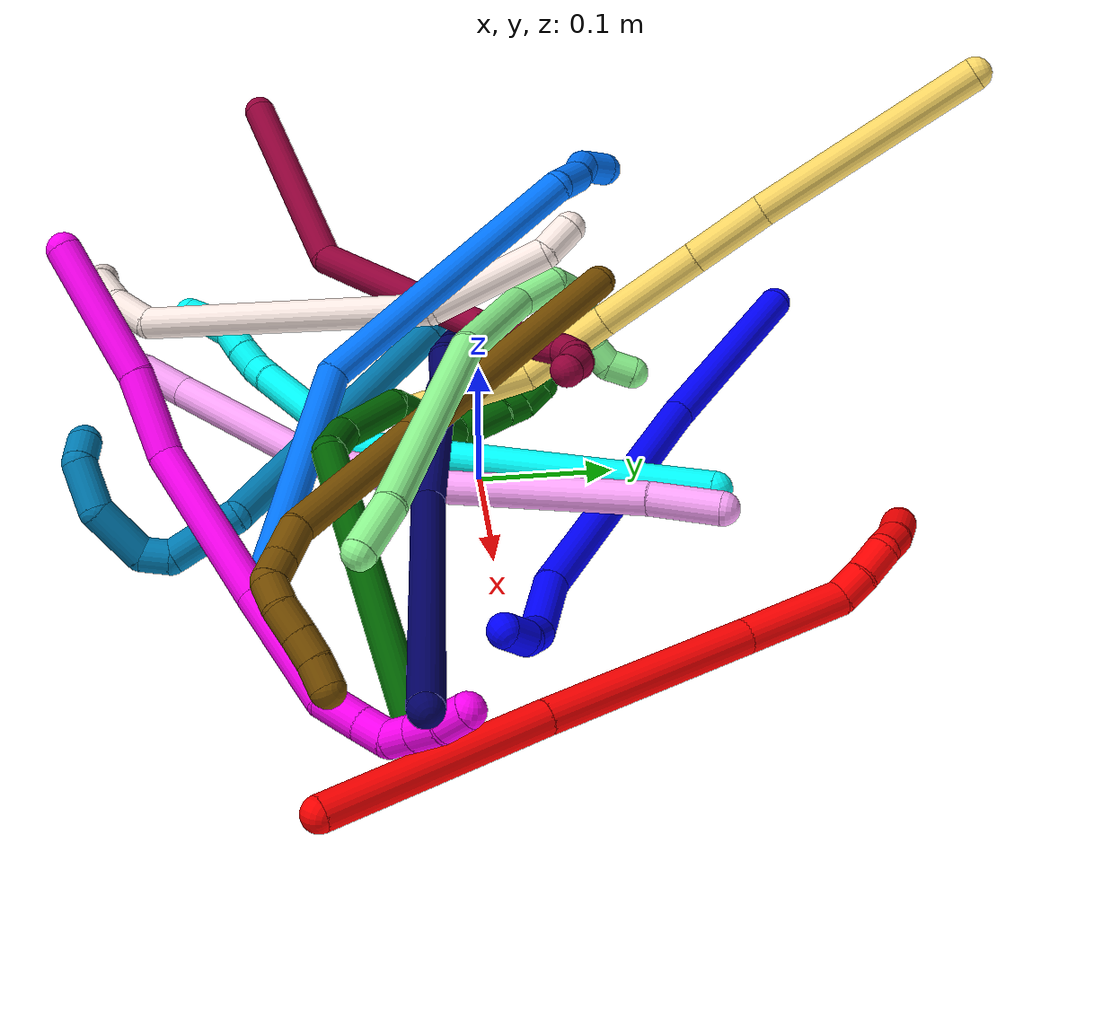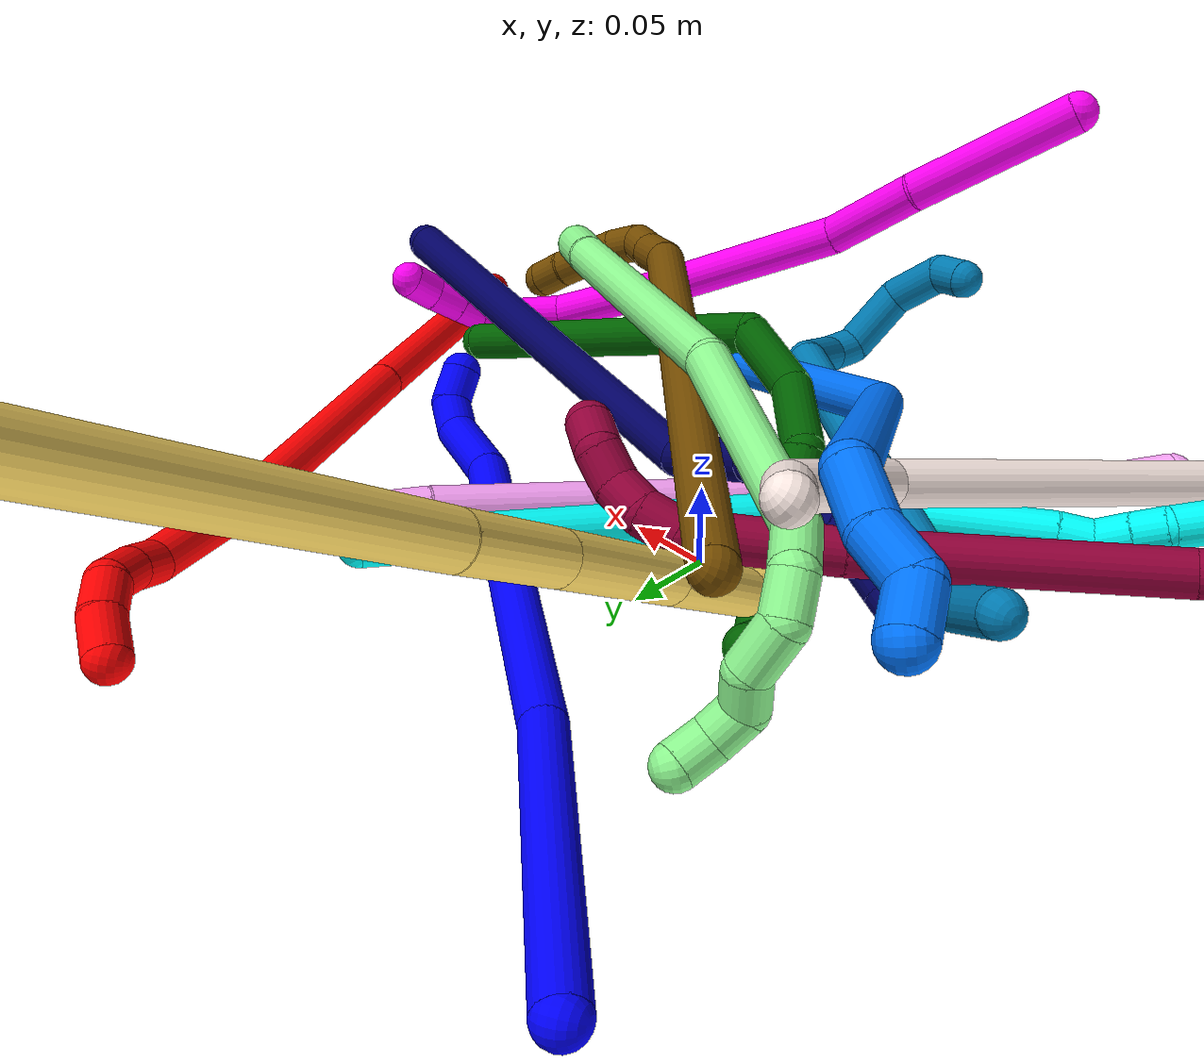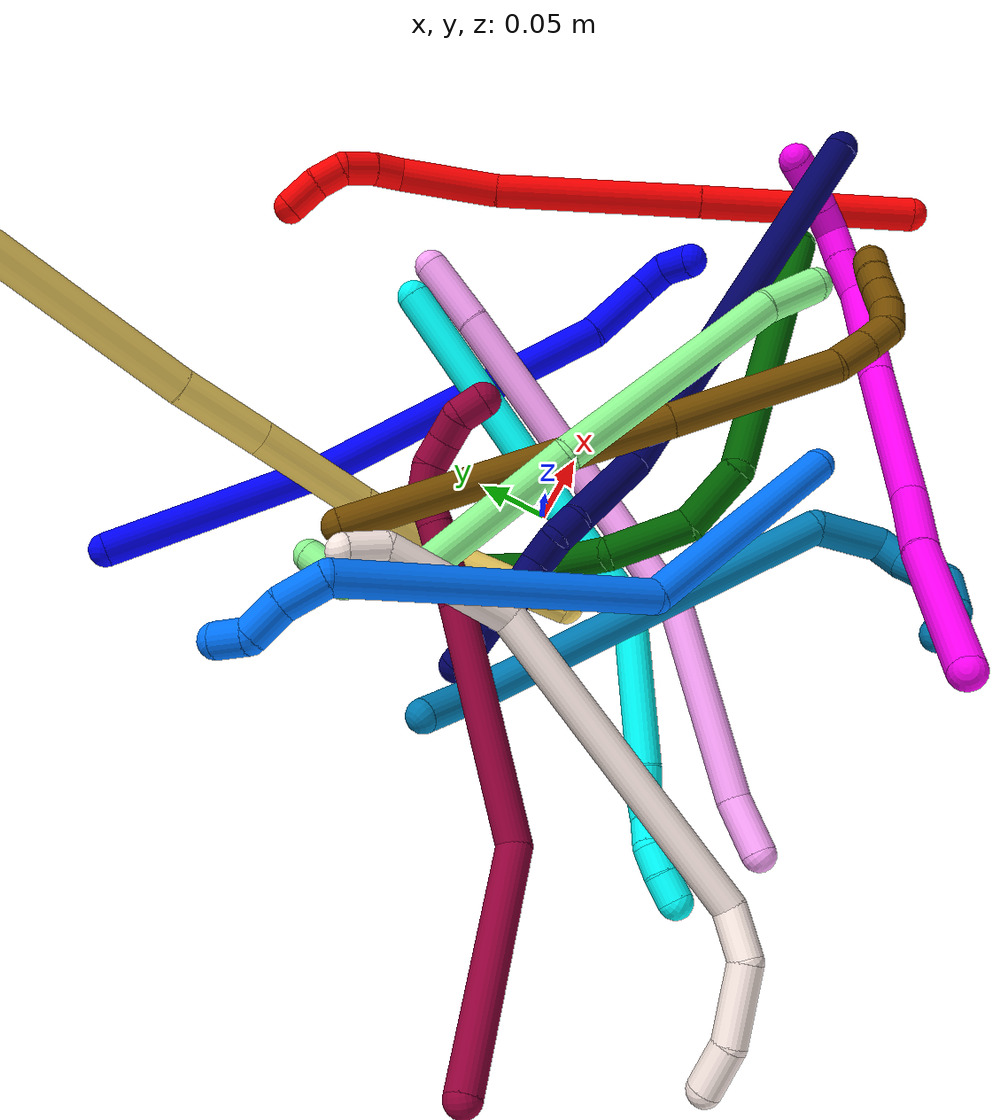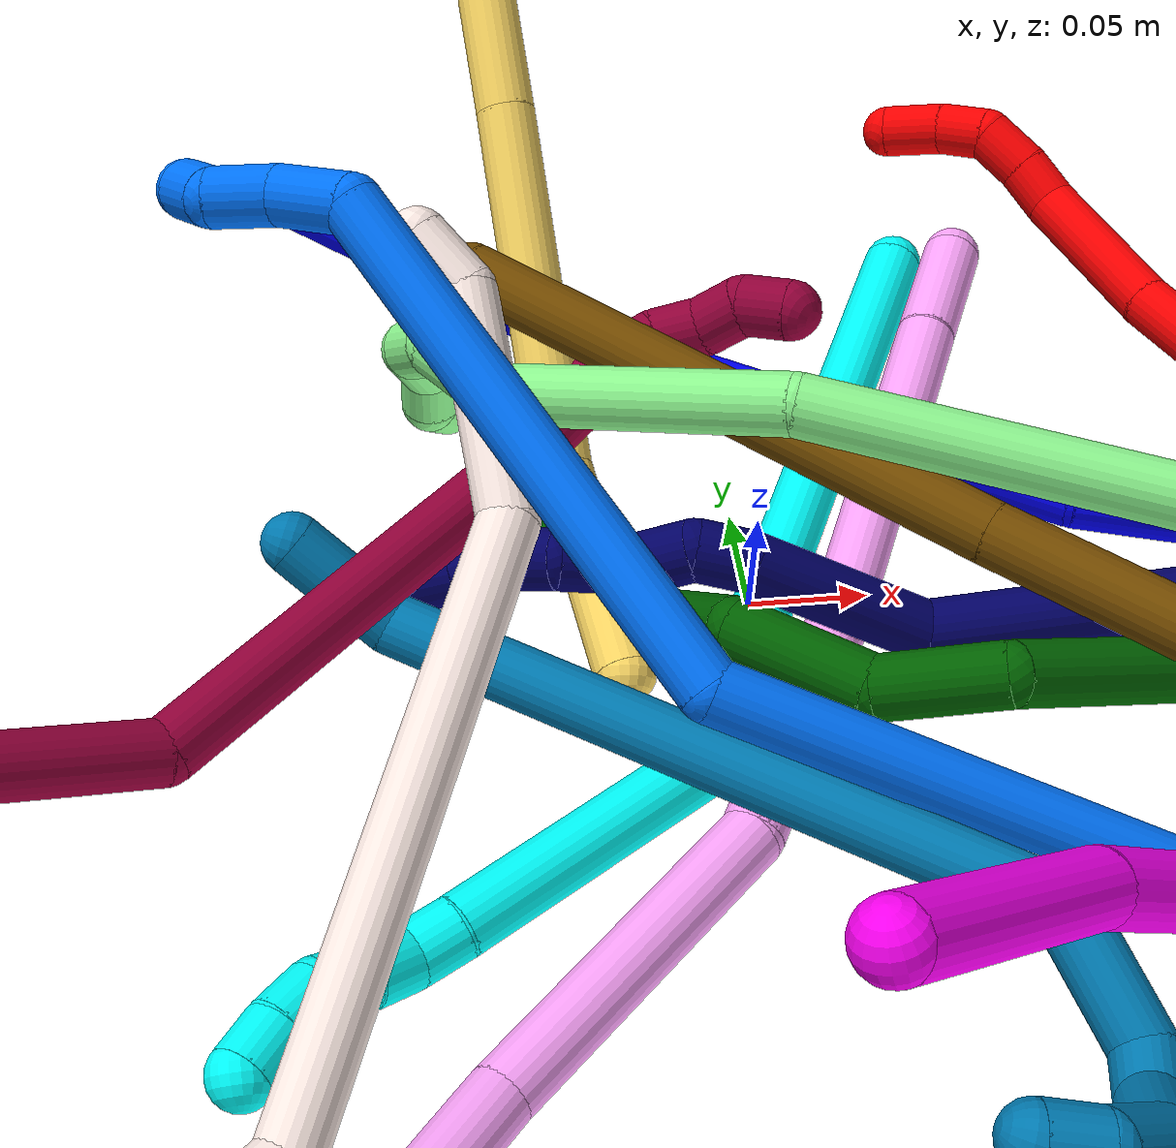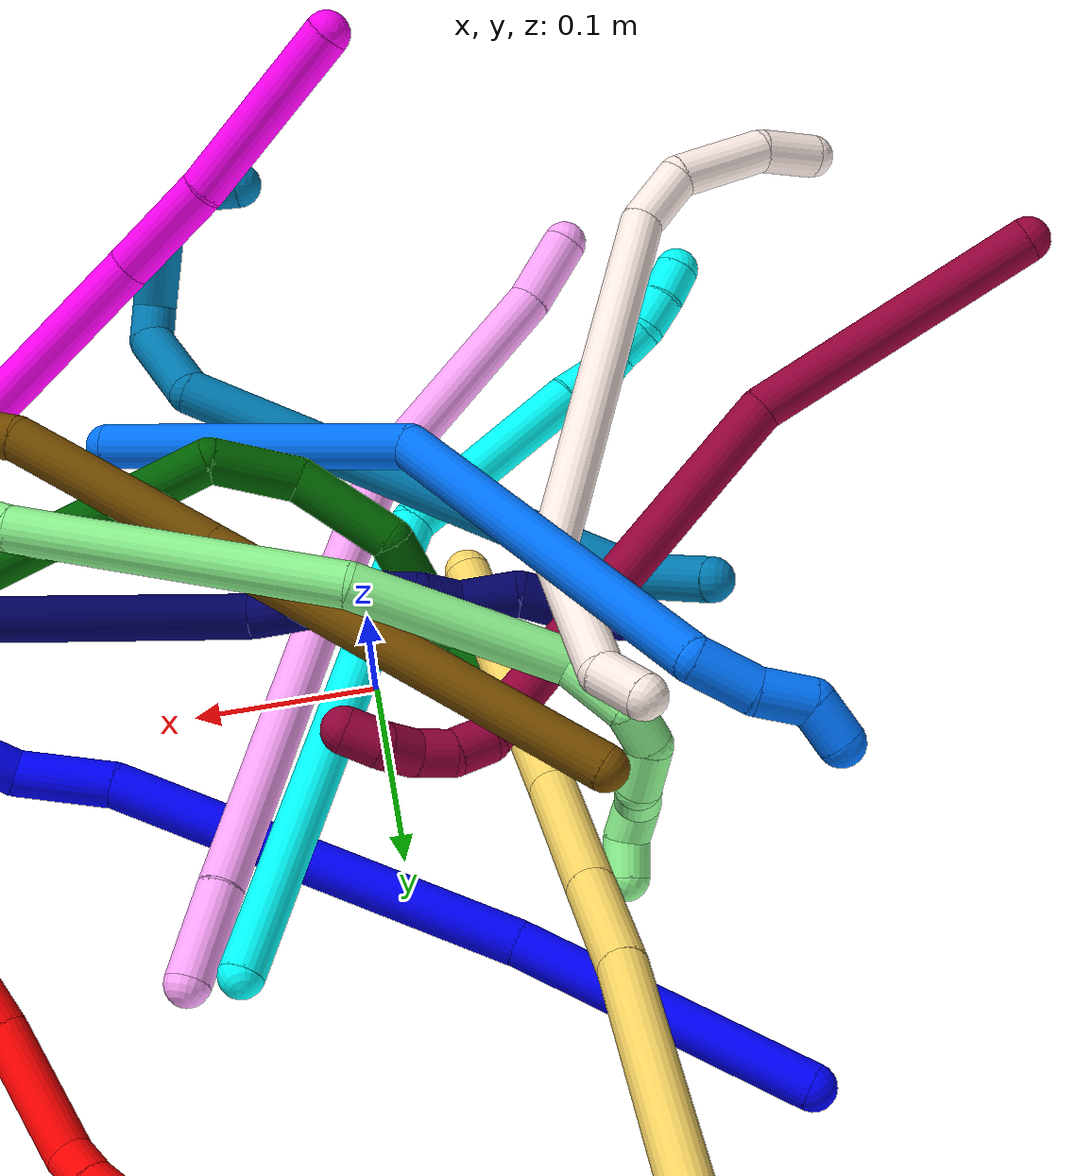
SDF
<sdf version="1.7">
 <world name="default">
  <plugin name="TubeGeneratorPlugin" filename="libtube_generator_plugin.so"/>
  <model name="photoneo_s_sensor">
   <static>1</static>
   <pose>0 0 2 1.57079 1.57079 3.14159</pose>
   <link name="link">
    <inertial><mass>0.1</mass></inertial>
    <sensor name="sensor" type="depth">
     <update_rate>30</update_rate>
     <camera>
      <horizontal_fov>1.22</horizontal_fov>
      <image><width>1920</width><height>1200</height><format>B8G8R8</format></image>
      <clip><near>0.1</near><far>4</far></clip>
      <depth_camera><output>points</output></depth_camera>
     </camera>
     <plugin name="camera_plugin" filename="libgazebo_ros_depth_camera.so">
      <baseline>0.2</baseline>
      <alwaysOn>1</alwaysOn>
      <updateRate>0.0</updateRate>
      <cameraName>camera_ir</cameraName>
      <imageTopicName>/camera/color/image_raw</imageTopicName>
      <cameraInfoTopicName>/camera/color/camera_info</cameraInfoTopicName>
      <depthImageTopicName>/camera/depth/image_raw</depthImageTopicName>
      <depthImageCameraInfoTopicName>/camera/depth/camera_info</depthImageCameraInfoTopicName>
      <pointCloudTopicName>/camera/depth/points</pointCloudTopicName>
      <frameName>fr_optical</frameName>
      <pointCloudCutoff>0.1</pointCloudCutoff>
      <pointCloudCutoffMax>2.0</pointCloudCutoffMax>
      <distortionK1>0</distortionK1>
      <distortionK2>0</distortionK2>
      <distortionK3>0</distortionK3>
      <distortionT1>0</distortionT1>
      <distortionT2>0</distortionT2>
      <CxPrime>0</CxPrime>
      <Cx>0</Cx>
      <Cy>0</Cy>
      <focalLength>0</focalLength>
      <hackBaseline>0</hackBaseline>
     </plugin>
    </sensor>
   </link>
  </model>
  <gravity>0 0 -9.8</gravity>
  <magnetic_field>6e-06 2.3e-05 -4.2e-05</magnetic_field>
  <atmosphere type="adiabatic"/>
  <physics name="default_physics" default="0" type="ode">
   <max_step_size>0.003</max_step_size>
   <real_time_factor>1</real_time_factor>
   <real_time_update_rate>1000</real_time_update_rate>
   <max_contacts>10000</max_contacts>
   <ode>
    <solver>
     <type>quick</type>
     <iters>100</iters>
     <sor>1.3</sor>
     <use_dynamic_moi_rescaling>0</use_dynamic_moi_rescaling>
    </solver>
    <constraints>
     <contact_max_correcting_vel>0</contact_max_correcting_vel>
     <contact_surface_layer>0.001</contact_surface_layer>
     <cfm>0</cfm>
     <erp>0.2</erp>
    </constraints>
   </ode>
  </physics>
  <scene><ambient>0.4 0.4 0.4 1</ambient><background>0.7 0.7 0.7 1</background><shadows>0</shadows></scene>
  <audio><device>default</device></audio>
  <spherical_coordinates>
   <surface_model>EARTH_WGS84</surface_model>
   <latitude_deg>0</latitude_deg>
   <longitude_deg>0</longitude_deg>
   <elevation>0</elevation>
   <heading_deg>0</heading_deg>
  </spherical_coordinates>
  <model name="bin">
   <static>1</static>
   <link name="bottom">
    <collision name="collision-bottom">
     <pose>0 0 -0.01 0 -0 0</pose>
     <geometry><box><size>0.8 0.6 0.02</size></box></geometry>
     <surface>
      <friction><ode><mu>100</mu><mu2>100</mu2></ode></friction>
      <contact><collide_bitmask>65535</collide_bitmask></contact>
     </surface>
    </collision>
   </link>
   <link name="west_wall">
    <collision name="collision-west_wall">
     <pose>-0.41 0 0.1 0 -0 0</pose>
     <geometry><box><size>0.02 0.6 0.2</size></box></geometry>
     <surface>
      <friction><ode><mu>100</mu><mu2>100</mu2></ode></friction>
      <contact><collide_bitmask>65535</collide_bitmask></contact>
     </surface>
    </collision>
   </link>
   <link name="east_wall">
    <collision name="collision-east_wall">
     <pose>0.41 0 0.1 0 -0 0</pose>
     <geometry><box><size>0.02 0.6 0.2</size></box></geometry>
     <surface>
      <friction><ode><mu>100</mu><mu2>100</mu2></ode></friction>
      <contact><collide_bitmask>65535</collide_bitmask></contact>
     </surface>
    </collision>
   </link>
   <link name="south_wall">
    <collision name="collision-south_wall">
     <pose>0 -0.31 0.1 0 -0 0</pose>
     <geometry><box><size>0.8 0.02 0.2</size></box></geometry>
     <surface>
      <friction><ode><mu>100</mu><mu2>100</mu2></ode></friction>
      <contact><collide_bitmask>65535</collide_bitmask></contact>
     </surface>
    </collision>
   </link>
   <link name="north_wall">
    <collision name="collision-north_wall">
     <pose>0 0.31 0.1 0 -0 0</pose>
     <geometry><box><size>0.8 0.02 0.2</size></box></geometry>
     <surface>
      <friction><ode><mu>100</mu><mu2>100</mu2></ode></friction>
      <contact><collide_bitmask>65535</collide_bitmask></contact>
     </surface>
    </collision>
   </link>
  </model>
  <model name="1">
   <static>0</static>
   <link name="1">
    <collision name="collision-cylinder-e_1_1_4">
     <pose>0.070437 -0.018913 0.04232 0.420274 0.988752 0.228926</pose>
     <geometry><cylinder><radius>0.0125</radius><length>0.168642</length></cylinder></geometry>
     <surface>
      <friction><ode><mu>1.16</mu><mu2>1.16</mu2><slip1>0</slip1><slip2>0</slip2></ode></friction>
      <contact><ode><kp>1e+06</kp><kd>1</kd><max_vel>0</max_vel><min_depth>0.001</min_depth></ode></contact>
     </surface>
    </collision>
    <visual name="visual-cylinder-e_1_1_4">
     <pose>0.070437 -0.018913 0.04232 0.420274 0.988752 0.228926</pose>
     <geometry><cylinder><radius>0.0125</radius><length>0.168642</length></cylinder></geometry>
     <material><ambient>0 0 1 1</ambient></material>
    </visual>
    <collision name="collision-cylinder-e_2_4_5">
     <pose>0.229159 -0.072352 0.151848 0.474563 0.862929 0.221768</pose>
     <geometry><cylinder><radius>0.0125</radius><length>0.232406</length></cylinder></geometry>
     <surface>
      <friction><ode><mu>1.16</mu><mu2>1.16</mu2><slip1>0</slip1><slip2>0</slip2></ode></friction>
      <contact><ode><kp>1e+06</kp><kd>1</kd><max_vel>0</max_vel><min_depth>0.001</min_depth></ode></contact>
     </surface>
    </collision>
    <visual name="visual-cylinder-e_2_4_5">
     <pose>0.229159 -0.072352 0.151848 0.474563 0.862929 0.221768</pose>
     <geometry><cylinder><radius>0.0125</radius><length>0.232406</length></cylinder></geometry>
     <material><ambient>0 0 1 1</ambient></material>
    </visual>
    <collision name="collision-cylinder-e_3_5_6">
     <pose>0.333214 -0.114386 0.239742 0.348195 0.621769 0.1129</pose>
     <geometry><cylinder><radius>0.0125</radius><length>0.054149</length></cylinder></geometry>
     <surface>
      <friction><ode><mu>1.16</mu><mu2>1.16</mu2><slip1>0</slip1><slip2>0</slip2></ode></friction>
      <contact><ode><kp>1e+06</kp><kd>1</kd><max_vel>0</max_vel><min_depth>0.001</min_depth></ode></contact>
     </surface>
    </collision>
    <visual name="visual-cylinder-e_3_5_6">
     <pose>0.333214 -0.114386 0.239742 0.348195 0.621769 0.1129</pose>
     <geometry><cylinder><radius>0.0125</radius><length>0.054149</length></cylinder></geometry>
     <material><ambient>0 0 1 1</ambient></material>
    </visual>
    <collision name="collision-cylinder-e_4_6_7">
     <pose>0.354595 -0.129693 0.266016 0.949073 0.529192 0.276589</pose>
     <geometry><cylinder><radius>0.0125</radius><length>0.022226</length></cylinder></geometry>
     <surface>
      <friction><ode><mu>1.16</mu><mu2>1.16</mu2><slip1>0</slip1><slip2>0</slip2></ode></friction>
      <contact><ode><kp>1e+06</kp><kd>1</kd><max_vel>0</max_vel><min_depth>0.001</min_depth></ode></contact>
     </surface>
    </collision>
    <visual name="visual-cylinder-e_4_6_7">
     <pose>0.354595 -0.129693 0.266016 0.949073 0.529192 0.276589</pose>
     <geometry><cylinder><radius>0.0125</radius><length>0.022226</length></cylinder></geometry>
     <material><ambient>0 0 1 1</ambient></material>
    </visual>
    <collision name="collision-cylinder-e_5_7_2">
     <pose>0.366682 -0.146725 0.271142 1.6207 0.611125 0.640362</pose>
     <geometry><cylinder><radius>0.0125</radius><length>0.022577</length></cylinder></geometry>
     <surface>
      <friction><ode><mu>1.16</mu><mu2>1.16</mu2><slip1>0</slip1><slip2>0</slip2></ode></friction>
      <contact><ode><kp>1e+06</kp><kd>1</kd><max_vel>0</max_vel><min_depth>0.001</min_depth></ode></contact>
     </surface>
    </collision>
    <visual name="visual-cylinder-e_5_7_2">
     <pose>0.366682 -0.146725 0.271142 1.6207 0.611125 0.640362</pose>
     <geometry><cylinder><radius>0.0125</radius><length>0.022577</length></cylinder></geometry>
     <material><ambient>0 0 1 1</ambient></material>
    </visual>
    <collision name="collision-sphere-2">
     <pose>0.373159 -0.155959 0.270681 0 -0 0</pose>
     <geometry><sphere><radius>0.0125</radius></sphere></geometry>
     <surface>
      <friction><ode><mu>1.16</mu><mu2>1.16</mu2><slip1>0</slip1><slip2>0</slip2></ode></friction>
      <contact><ode><kp>1e+06</kp><kd>1</kd><max_vel>0</max_vel><min_depth>0.001</min_depth></ode></contact>
     </surface>
    </collision>
    <visual name="visual-sphere-2">
     <pose>0.373159 -0.155959 0.270681 0 -0 0</pose>
     <geometry><sphere><radius>0.0125</radius></sphere></geometry>
     <material><ambient>0 0 1 1</ambient></material>
    </visual>
    <collision name="collision-sphere-7">
     <pose>0.360205 -0.137491 0.271603 0 -0 0</pose>
     <geometry><sphere><radius>0.0125</radius></sphere></geometry>
     <surface>
      <friction><ode><mu>1.16</mu><mu2>1.16</mu2><slip1>0</slip1><slip2>0</slip2></ode></friction>
      <contact><ode><kp>1e+06</kp><kd>1</kd><max_vel>0</max_vel><min_depth>0.001</min_depth></ode></contact>
     </surface>
    </collision>
    <visual name="visual-sphere-7">
     <pose>0.360205 -0.137491 0.271603 0 -0 0</pose>
     <geometry><sphere><radius>0.0125</radius></sphere></geometry>
     <material><ambient>0 0 1 1</ambient></material>
    </visual>
    <collision name="collision-sphere-6">
     <pose>0.348984 -0.121895 0.260429 0 -0 0</pose>
     <geometry><sphere><radius>0.0125</radius></sphere></geometry>
     <surface>
      <friction><ode><mu>1.16</mu><mu2>1.16</mu2><slip1>0</slip1><slip2>0</slip2></ode></friction>
      <contact><ode><kp>1e+06</kp><kd>1</kd><max_vel>0</max_vel><min_depth>0.001</min_depth></ode></contact>
     </surface>
    </collision>
    <visual name="visual-sphere-6">
     <pose>0.348984 -0.121895 0.260429 0 -0 0</pose>
     <geometry><sphere><radius>0.0125</radius></sphere></geometry>
     <material><ambient>0 0 1 1</ambient></material>
    </visual>
    <collision name="collision-sphere-5">
     <pose>0.317444 -0.106877 0.219055 0 -0 0</pose>
     <geometry><sphere><radius>0.0125</radius></sphere></geometry>
     <surface>
      <friction><ode><mu>1.16</mu><mu2>1.16</mu2><slip1>0</slip1><slip2>0</slip2></ode></friction>
      <contact><ode><kp>1e+06</kp><kd>1</kd><max_vel>0</max_vel><min_depth>0.001</min_depth></ode></contact>
     </surface>
    </collision>
    <visual name="visual-sphere-5">
     <pose>0.317444 -0.106877 0.219055 0 -0 0</pose>
     <geometry><sphere><radius>0.0125</radius></sphere></geometry>
     <material><ambient>0 0 1 1</ambient></material>
    </visual>
    <collision name="collision-sphere-1">
     <geometry><sphere><radius>0.0125</radius></sphere></geometry>
     <surface>
      <friction><ode><mu>1.16</mu><mu2>1.16</mu2><slip1>0</slip1><slip2>0</slip2></ode></friction>
      <contact><ode><kp>1e+06</kp><kd>1</kd><max_vel>0</max_vel><min_depth>0.001</min_depth></ode></contact>
     </surface>
    </collision>
    <visual name="visual-sphere-1">
     <geometry><sphere><radius>0.0125</radius></sphere></geometry>
     <material><ambient>0 0 1 1</ambient></material>
    </visual>
    <collision name="collision-sphere-4">
     <pose>0.140873 -0.037826 0.08464 0 -0 0</pose>
     <geometry><sphere><radius>0.0125</radius></sphere></geometry>
     <surface>
      <friction><ode><mu>1.16</mu><mu2>1.16</mu2><slip1>0</slip1><slip2>0</slip2></ode></friction>
      <contact><ode><kp>1e+06</kp><kd>1</kd><max_vel>0</max_vel><min_depth>0.001</min_depth></ode></contact>
     </surface>
    </collision>
    <visual name="visual-sphere-4">
     <pose>0.140873 -0.037826 0.08464 0 -0 0</pose>
     <geometry><sphere><radius>0.0125</radius></sphere></geometry>
     <material><ambient>0 0 1 1</ambient></material>
    </visual>
    <inertial>
     <pose>0.198679 -0.064787 0.134886 0 -0 0</pose>
     <mass>0.5</mass>
     <inertia>
      <ixx>0.001135</ixx>
      <ixy>0</ixy>
      <ixz>0</ixz>
      <iyy>0.001597</iyy>
      <iyz>0</iyz>
      <izz>-0.000719</izz>
     </inertia>
    </inertial>
   </link>
   <pose>-0.183557 0.261952 0.024733 -1.71955 0.267361 -1.22346</pose>
  </model>
  <model name="2">
   <static>0</static>
   <link name="2">
    <collision name="collision-cylinder-e_1_1_4">
     <pose>-0.028417 0.07416 0.022907 -1.27121 -0.35096 0.26013</pose>
     <geometry><cylinder><radius>0.0125</radius><length>0.165312</length></cylinder></geometry>
     <surface>
      <friction><ode><mu>1.16</mu><mu2>1.16</mu2><slip1>0</slip1><slip2>0</slip2></ode></friction>
      <contact><ode><kp>1e+06</kp><kd>1</kd><max_vel>0</max_vel><min_depth>0.001</min_depth></ode></contact>
     </surface>
    </collision>
    <visual name="visual-cylinder-e_1_1_4">
     <pose>-0.028417 0.07416 0.022907 -1.27121 -0.35096 0.26013</pose>
     <geometry><cylinder><radius>0.0125</radius><length>0.165312</length></cylinder></geometry>
     <material><ambient>1 0 0 1</ambient></material>
    </visual>
    <collision name="collision-cylinder-e_2_4_5">
     <pose>-0.082814 0.220427 0.067933 -1.27314 -0.331733 0.246249</pose>
     <geometry><cylinder><radius>0.0125</radius><length>0.159544</length></cylinder></geometry>
     <surface>
      <friction><ode><mu>1.16</mu><mu2>1.16</mu2><slip1>0</slip1><slip2>0</slip2></ode></friction>
      <contact><ode><kp>1e+06</kp><kd>1</kd><max_vel>0</max_vel><min_depth>0.001</min_depth></ode></contact>
     </surface>
    </collision>
    <visual name="visual-cylinder-e_2_4_5">
     <pose>-0.082814 0.220427 0.067933 -1.27314 -0.331733 0.246249</pose>
     <geometry><cylinder><radius>0.0125</radius><length>0.159544</length></cylinder></geometry>
     <material><ambient>1 0 0 1</ambient></material>
    </visual>
    <collision name="collision-cylinder-e_3_5_6">
     <pose>-0.123238 0.325096 0.103883 -1.16916 -0.387606 0.258306</pose>
     <geometry><cylinder><radius>0.0125</radius><length>0.076426</length></cylinder></geometry>
     <surface>
      <friction><ode><mu>1.16</mu><mu2>1.16</mu2><slip1>0</slip1><slip2>0</slip2></ode></friction>
      <contact><ode><kp>1e+06</kp><kd>1</kd><max_vel>0</max_vel><min_depth>0.001</min_depth></ode></contact>
     </surface>
    </collision>
    <visual name="visual-cylinder-e_3_5_6">
     <pose>-0.123238 0.325096 0.103883 -1.16916 -0.387606 0.258306</pose>
     <geometry><cylinder><radius>0.0125</radius><length>0.076426</length></cylinder></geometry>
     <material><ambient>1 0 0 1</ambient></material>
    </visual>
    <collision name="collision-cylinder-e_4_6_7">
     <pose>-0.145677 0.365188 0.120355 -1.23335 -0.786359 0.571954</pose>
     <geometry><cylinder><radius>0.0125</radius><length>0.022591</length></cylinder></geometry>
     <surface>
      <friction><ode><mu>1.16</mu><mu2>1.16</mu2><slip1>0</slip1><slip2>0</slip2></ode></friction>
      <contact><ode><kp>1e+06</kp><kd>1</kd><max_vel>0</max_vel><min_depth>0.001</min_depth></ode></contact>
     </surface>
    </collision>
    <visual name="visual-cylinder-e_4_6_7">
     <pose>-0.145677 0.365188 0.120355 -1.23335 -0.786359 0.571954</pose>
     <geometry><cylinder><radius>0.0125</radius><length>0.022591</length></cylinder></geometry>
     <material><ambient>1 0 0 1</ambient></material>
    </visual>
    <collision name="collision-cylinder-e_5_7_8">
     <pose>-0.162231 0.381701 0.123956 -1.46439 -0.758393 0.687896</pose>
     <geometry><cylinder><radius>0.0125</radius><length>0.024891</length></cylinder></geometry>
     <surface>
      <friction><ode><mu>1.16</mu><mu2>1.16</mu2><slip1>0</slip1><slip2>0</slip2></ode></friction>
      <contact><ode><kp>1e+06</kp><kd>1</kd><max_vel>0</max_vel><min_depth>0.001</min_depth></ode></contact>
     </surface>
    </collision>
    <visual name="visual-cylinder-e_5_7_8">
     <pose>-0.162231 0.381701 0.123956 -1.46439 -0.758393 0.687896</pose>
     <geometry><cylinder><radius>0.0125</radius><length>0.024891</length></cylinder></geometry>
     <material><ambient>1 0 0 1</ambient></material>
    </visual>
    <collision name="collision-cylinder-e_6_8_9">
     <pose>-0.173616 0.401691 0.121938 -1.83505 -0.242912 0.31628</pose>
     <geometry><cylinder><radius>0.0125</radius><length>0.023494</length></cylinder></geometry>
     <surface>
      <friction><ode><mu>1.16</mu><mu2>1.16</mu2><slip1>0</slip1><slip2>0</slip2></ode></friction>
      <contact><ode><kp>1e+06</kp><kd>1</kd><max_vel>0</max_vel><min_depth>0.001</min_depth></ode></contact>
     </surface>
    </collision>
    <visual name="visual-cylinder-e_6_8_9">
     <pose>-0.173616 0.401691 0.121938 -1.83505 -0.242912 0.31628</pose>
     <geometry><cylinder><radius>0.0125</radius><length>0.023494</length></cylinder></geometry>
     <material><ambient>1 0 0 1</ambient></material>
    </visual>
    <collision name="collision-cylinder-e_7_9_2">
     <pose>-0.179036 0.424736 0.112577 -2.05828 -0.188151 0.311098</pose>
     <geometry><cylinder><radius>0.0125</radius><length>0.027743</length></cylinder></geometry>
     <surface>
      <friction><ode><mu>1.16</mu><mu2>1.16</mu2><slip1>0</slip1><slip2>0</slip2></ode></friction>
      <contact><ode><kp>1e+06</kp><kd>1</kd><max_vel>0</max_vel><min_depth>0.001</min_depth></ode></contact>
     </surface>
    </collision>
    <visual name="visual-cylinder-e_7_9_2">
     <pose>-0.179036 0.424736 0.112577 -2.05828 -0.188151 0.311098</pose>
     <geometry><cylinder><radius>0.0125</radius><length>0.027743</length></cylinder></geometry>
     <material><ambient>1 0 0 1</ambient></material>
    </visual>
    <collision name="collision-sphere-2">
     <pose>-0.18163 0.436776 0.106194 0 -0 0</pose>
     <geometry><sphere><radius>0.0125</radius></sphere></geometry>
     <surface>
      <friction><ode><mu>1.16</mu><mu2>1.16</mu2><slip1>0</slip1><slip2>0</slip2></ode></friction>
      <contact><ode><kp>1e+06</kp><kd>1</kd><max_vel>0</max_vel><min_depth>0.001</min_depth></ode></contact>
     </surface>
    </collision>
    <visual name="visual-sphere-2">
     <pose>-0.18163 0.436776 0.106194 0 -0 0</pose>
     <geometry><sphere><radius>0.0125</radius></sphere></geometry>
     <material><ambient>1 0 0 1</ambient></material>
    </visual>
    <collision name="collision-sphere-9">
     <pose>-0.176441 0.412697 0.11896 0 -0 0</pose>
     <geometry><sphere><radius>0.0125</radius></sphere></geometry>
     <surface>
      <friction><ode><mu>1.16</mu><mu2>1.16</mu2><slip1>0</slip1><slip2>0</slip2></ode></friction>
      <contact><ode><kp>1e+06</kp><kd>1</kd><max_vel>0</max_vel><min_depth>0.001</min_depth></ode></contact>
     </surface>
    </collision>
    <visual name="visual-sphere-9">
     <pose>-0.176441 0.412697 0.11896 0 -0 0</pose>
     <geometry><sphere><radius>0.0125</radius></sphere></geometry>
     <material><ambient>1 0 0 1</ambient></material>
    </visual>
    <collision name="collision-sphere-4">
     <pose>-0.056834 0.14832 0.045813 0 -0 0</pose>
     <geometry><sphere><radius>0.0125</radius></sphere></geometry>
     <surface>
      <friction><ode><mu>1.16</mu><mu2>1.16</mu2><slip1>0</slip1><slip2>0</slip2></ode></friction>
      <contact><ode><kp>1e+06</kp><kd>1</kd><max_vel>0</max_vel><min_depth>0.001</min_depth></ode></contact>
     </surface>
    </collision>
    <visual name="visual-sphere-4">
     <pose>-0.056834 0.14832 0.045813 0 -0 0</pose>
     <geometry><sphere><radius>0.0125</radius></sphere></geometry>
     <material><ambient>1 0 0 1</ambient></material>
    </visual>
    <collision name="collision-sphere-1">
     <geometry><sphere><radius>0.0125</radius></sphere></geometry>
     <surface>
      <friction><ode><mu>1.16</mu><mu2>1.16</mu2><slip1>0</slip1><slip2>0</slip2></ode></friction>
      <contact><ode><kp>1e+06</kp><kd>1</kd><max_vel>0</max_vel><min_depth>0.001</min_depth></ode></contact>
     </surface>
    </collision>
    <visual name="visual-sphere-1">
     <geometry><sphere><radius>0.0125</radius></sphere></geometry>
     <material><ambient>1 0 0 1</ambient></material>
    </visual>
    <collision name="collision-sphere-8">
     <pose>-0.17079 0.390685 0.124916 0 -0 0</pose>
     <geometry><sphere><radius>0.0125</radius></sphere></geometry>
     <surface>
      <friction><ode><mu>1.16</mu><mu2>1.16</mu2><slip1>0</slip1><slip2>0</slip2></ode></friction>
      <contact><ode><kp>1e+06</kp><kd>1</kd><max_vel>0</max_vel><min_depth>0.001</min_depth></ode></contact>
     </surface>
    </collision>
    <visual name="visual-sphere-8">
     <pose>-0.17079 0.390685 0.124916 0 -0 0</pose>
     <geometry><sphere><radius>0.0125</radius></sphere></geometry>
     <material><ambient>1 0 0 1</ambient></material>
    </visual>
    <collision name="collision-sphere-5">
     <pose>-0.108795 0.292533 0.090053 0 -0 0</pose>
     <geometry><sphere><radius>0.0125</radius></sphere></geometry>
     <surface>
      <friction><ode><mu>1.16</mu><mu2>1.16</mu2><slip1>0</slip1><slip2>0</slip2></ode></friction>
      <contact><ode><kp>1e+06</kp><kd>1</kd><max_vel>0</max_vel><min_depth>0.001</min_depth></ode></contact>
     </surface>
    </collision>
    <visual name="visual-sphere-5">
     <pose>-0.108795 0.292533 0.090053 0 -0 0</pose>
     <geometry><sphere><radius>0.0125</radius></sphere></geometry>
     <material><ambient>1 0 0 1</ambient></material>
    </visual>
    <collision name="collision-sphere-6">
     <pose>-0.137682 0.357658 0.117713 0 -0 0</pose>
     <geometry><sphere><radius>0.0125</radius></sphere></geometry>
     <surface>
      <friction><ode><mu>1.16</mu><mu2>1.16</mu2><slip1>0</slip1><slip2>0</slip2></ode></friction>
      <contact><ode><kp>1e+06</kp><kd>1</kd><max_vel>0</max_vel><min_depth>0.001</min_depth></ode></contact>
     </surface>
    </collision>
    <visual name="visual-sphere-6">
     <pose>-0.137682 0.357658 0.117713 0 -0 0</pose>
     <geometry><sphere><radius>0.0125</radius></sphere></geometry>
     <material><ambient>1 0 0 1</ambient></material>
    </visual>
    <collision name="collision-sphere-7">
     <pose>-0.153671 0.372718 0.122997 0 -0 0</pose>
     <geometry><sphere><radius>0.0125</radius></sphere></geometry>
     <surface>
      <friction><ode><mu>1.16</mu><mu2>1.16</mu2><slip1>0</slip1><slip2>0</slip2></ode></friction>
      <contact><ode><kp>1e+06</kp><kd>1</kd><max_vel>0</max_vel><min_depth>0.001</min_depth></ode></contact>
     </surface>
    </collision>
    <visual name="visual-sphere-7">
     <pose>-0.153671 0.372718 0.122997 0 -0 0</pose>
     <geometry><sphere><radius>0.0125</radius></sphere></geometry>
     <material><ambient>1 0 0 1</ambient></material>
    </visual>
    <inertial>
     <pose>-0.087407 0.222489 0.068713 0 -0 0</pose>
     <mass>0.5</mass>
     <inertia>
      <ixx>0.000877</ixx>
      <ixy>0</ixy>
      <ixz>0</ixz>
      <iyy>0.000504</iyy>
      <iyz>0</iyz>
      <izz>-0.000425</izz>
     </inertia>
    </inertial>
   </link>
   <pose>0.355545 -0.135588 0.011497 -1.11576 1.11723 -0.430069</pose>
  </model>
  <model name="3">
   <static>0</static>
   <link name="3">
    <collision name="collision-cylinder-e_1_1_4">
     <pose>-0.031944 -0.07052 0.117905 0.539028 -0.228454 -0.063362</pose>
     <geometry><cylinder><radius>0.0125</radius><length>0.282101</length></cylinder></geometry>
     <surface>
      <friction><ode><mu>1.16</mu><mu2>1.16</mu2><slip1>0</slip1><slip2>0</slip2></ode></friction>
      <contact><ode><kp>1e+06</kp><kd>1</kd><max_vel>0</max_vel><min_depth>0.001</min_depth></ode></contact>
     </surface>
    </collision>
    <visual name="visual-cylinder-e_1_1_4">
     <pose>-0.031944 -0.07052 0.117905 0.539028 -0.228454 -0.063362</pose>
     <geometry><cylinder><radius>0.0125</radius><length>0.282101</length></cylinder></geometry>
     <material><ambient>0.003922 1 0.996078 1</ambient></material>
    </visual>
    <collision name="collision-cylinder-e_2_4_5">
     <pose>-0.07341 -0.191939 0.261907 1.09703 -0.164963 -0.100946</pose>
     <geometry><cylinder><radius>0.0125</radius><length>0.115971</length></cylinder></geometry>
     <surface>
      <friction><ode><mu>1.16</mu><mu2>1.16</mu2><slip1>0</slip1><slip2>0</slip2></ode></friction>
      <contact><ode><kp>1e+06</kp><kd>1</kd><max_vel>0</max_vel><min_depth>0.001</min_depth></ode></contact>
     </surface>
    </collision>
    <visual name="visual-cylinder-e_2_4_5">
     <pose>-0.07341 -0.191939 0.261907 1.09703 -0.164963 -0.100946</pose>
     <geometry><cylinder><radius>0.0125</radius><length>0.115971</length></cylinder></geometry>
     <material><ambient>0.003922 1 0.996078 1</ambient></material>
    </visual>
    <collision name="collision-cylinder-e_3_5_6">
     <pose>-0.083462 -0.252233 0.292317 1.14033 -0.051206 -0.032837</pose>
     <geometry><cylinder><radius>0.0125</radius><length>0.020705</length></cylinder></geometry>
     <surface>
      <friction><ode><mu>1.16</mu><mu2>1.16</mu2><slip1>0</slip1><slip2>0</slip2></ode></friction>
      <contact><ode><kp>1e+06</kp><kd>1</kd><max_vel>0</max_vel><min_depth>0.001</min_depth></ode></contact>
     </surface>
    </collision>
    <visual name="visual-cylinder-e_3_5_6">
     <pose>-0.083462 -0.252233 0.292317 1.14033 -0.051206 -0.032837</pose>
     <geometry><cylinder><radius>0.0125</radius><length>0.020705</length></cylinder></geometry>
     <material><ambient>0.003922 1 0.996078 1</ambient></material>
    </visual>
    <collision name="collision-cylinder-e_4_6_7">
     <pose>-0.089098 -0.270141 0.29975 1.21964 -0.512919 -0.362401</pose>
     <geometry><cylinder><radius>0.0125</radius><length>0.020809</length></cylinder></geometry>
     <surface>
      <friction><ode><mu>1.16</mu><mu2>1.16</mu2><slip1>0</slip1><slip2>0</slip2></ode></friction>
      <contact><ode><kp>1e+06</kp><kd>1</kd><max_vel>0</max_vel><min_depth>0.001</min_depth></ode></contact>
     </surface>
    </collision>
    <visual name="visual-cylinder-e_4_6_7">
     <pose>-0.089098 -0.270141 0.29975 1.21964 -0.512919 -0.362401</pose>
     <geometry><cylinder><radius>0.0125</radius><length>0.020809</length></cylinder></geometry>
     <material><ambient>0.003922 1 0.996078 1</ambient></material>
    </visual>
    <collision name="collision-cylinder-e_5_7_8">
     <pose>-0.098939 -0.287257 0.305043 1.32329 -0.490176 -0.384735</pose>
     <geometry><cylinder><radius>0.0125</radius><length>0.020118</length></cylinder></geometry>
     <surface>
      <friction><ode><mu>1.16</mu><mu2>1.16</mu2><slip1>0</slip1><slip2>0</slip2></ode></friction>
      <contact><ode><kp>1e+06</kp><kd>1</kd><max_vel>0</max_vel><min_depth>0.001</min_depth></ode></contact>
     </surface>
    </collision>
    <visual name="visual-cylinder-e_5_7_8">
     <pose>-0.098939 -0.287257 0.305043 1.32329 -0.490176 -0.384735</pose>
     <geometry><cylinder><radius>0.0125</radius><length>0.020118</length></cylinder></geometry>
     <material><ambient>0.003922 1 0.996078 1</ambient></material>
    </visual>
    <collision name="collision-cylinder-e_6_8_9">
     <pose>-0.107585 -0.303147 0.313093 0.892126 -0.395745 -0.191174</pose>
     <geometry><cylinder><radius>0.0125</radius><length>0.020288</length></cylinder></geometry>
     <surface>
      <friction><ode><mu>1.16</mu><mu2>1.16</mu2><slip1>0</slip1><slip2>0</slip2></ode></friction>
      <contact><ode><kp>1e+06</kp><kd>1</kd><max_vel>0</max_vel><min_depth>0.001</min_depth></ode></contact>
     </surface>
    </collision>
    <visual name="visual-cylinder-e_6_8_9">
     <pose>-0.107585 -0.303147 0.313093 0.892126 -0.395745 -0.191174</pose>
     <geometry><cylinder><radius>0.0125</radius><length>0.020288</length></cylinder></geometry>
     <material><ambient>0.003922 1 0.996078 1</ambient></material>
    </visual>
    <collision name="collision-cylinder-e_7_9_2">
     <pose>-0.114895 -0.316842 0.325858 0.7493 -0.346658 -0.137479</pose>
     <geometry><cylinder><radius>0.0125</radius><length>0.020008</length></cylinder></geometry>
     <surface>
      <friction><ode><mu>1.16</mu><mu2>1.16</mu2><slip1>0</slip1><slip2>0</slip2></ode></friction>
      <contact><ode><kp>1e+06</kp><kd>1</kd><max_vel>0</max_vel><min_depth>0.001</min_depth></ode></contact>
     </surface>
    </collision>
    <visual name="visual-cylinder-e_7_9_2">
     <pose>-0.114895 -0.316842 0.325858 0.7493 -0.346658 -0.137479</pose>
     <geometry><cylinder><radius>0.0125</radius><length>0.020008</length></cylinder></geometry>
     <material><ambient>0.003922 1 0.996078 1</ambient></material>
    </visual>
    <collision name="collision-sphere-2">
     <pose>-0.118294 -0.323251 0.332747 0 -0 0</pose>
     <geometry><sphere><radius>0.0125</radius></sphere></geometry>
     <surface>
      <friction><ode><mu>1.16</mu><mu2>1.16</mu2><slip1>0</slip1><slip2>0</slip2></ode></friction>
      <contact><ode><kp>1e+06</kp><kd>1</kd><max_vel>0</max_vel><min_depth>0.001</min_depth></ode></contact>
     </surface>
    </collision>
    <visual name="visual-sphere-2">
     <pose>-0.118294 -0.323251 0.332747 0 -0 0</pose>
     <geometry><sphere><radius>0.0125</radius></sphere></geometry>
     <material><ambient>0.003922 1 0.996078 1</ambient></material>
    </visual>
    <collision name="collision-sphere-9">
     <pose>-0.111496 -0.310433 0.318969 0 -0 0</pose>
     <geometry><sphere><radius>0.0125</radius></sphere></geometry>
     <surface>
      <friction><ode><mu>1.16</mu><mu2>1.16</mu2><slip1>0</slip1><slip2>0</slip2></ode></friction>
      <contact><ode><kp>1e+06</kp><kd>1</kd><max_vel>0</max_vel><min_depth>0.001</min_depth></ode></contact>
     </surface>
    </collision>
    <visual name="visual-sphere-9">
     <pose>-0.111496 -0.310433 0.318969 0 -0 0</pose>
     <geometry><sphere><radius>0.0125</radius></sphere></geometry>
     <material><ambient>0.003922 1 0.996078 1</ambient></material>
    </visual>
    <collision name="collision-sphere-4">
     <pose>-0.063888 -0.141041 0.235811 0 -0 0</pose>
     <geometry><sphere><radius>0.0125</radius></sphere></geometry>
     <surface>
      <friction><ode><mu>1.16</mu><mu2>1.16</mu2><slip1>0</slip1><slip2>0</slip2></ode></friction>
      <contact><ode><kp>1e+06</kp><kd>1</kd><max_vel>0</max_vel><min_depth>0.001</min_depth></ode></contact>
     </surface>
    </collision>
    <visual name="visual-sphere-4">
     <pose>-0.063888 -0.141041 0.235811 0 -0 0</pose>
     <geometry><sphere><radius>0.0125</radius></sphere></geometry>
     <material><ambient>0.003922 1 0.996078 1</ambient></material>
    </visual>
    <collision name="collision-sphere-1">
     <geometry><sphere><radius>0.0125</radius></sphere></geometry>
     <surface>
      <friction><ode><mu>1.16</mu><mu2>1.16</mu2><slip1>0</slip1><slip2>0</slip2></ode></friction>
      <contact><ode><kp>1e+06</kp><kd>1</kd><max_vel>0</max_vel><min_depth>0.001</min_depth></ode></contact>
     </surface>
    </collision>
    <visual name="visual-sphere-1">
     <geometry><sphere><radius>0.0125</radius></sphere></geometry>
     <material><ambient>0.003922 1 0.996078 1</ambient></material>
    </visual>
    <collision name="collision-sphere-8">
     <pose>-0.103675 -0.295861 0.307217 0 -0 0</pose>
     <geometry><sphere><radius>0.0125</radius></sphere></geometry>
     <surface>
      <friction><ode><mu>1.16</mu><mu2>1.16</mu2><slip1>0</slip1><slip2>0</slip2></ode></friction>
      <contact><ode><kp>1e+06</kp><kd>1</kd><max_vel>0</max_vel><min_depth>0.001</min_depth></ode></contact>
     </surface>
    </collision>
    <visual name="visual-sphere-8">
     <pose>-0.103675 -0.295861 0.307217 0 -0 0</pose>
     <geometry><sphere><radius>0.0125</radius></sphere></geometry>
     <material><ambient>0.003922 1 0.996078 1</ambient></material>
    </visual>
    <collision name="collision-sphere-5">
     <pose>-0.082932 -0.242838 0.288003 0 -0 0</pose>
     <geometry><sphere><radius>0.0125</radius></sphere></geometry>
     <surface>
      <friction><ode><mu>1.16</mu><mu2>1.16</mu2><slip1>0</slip1><slip2>0</slip2></ode></friction>
      <contact><ode><kp>1e+06</kp><kd>1</kd><max_vel>0</max_vel><min_depth>0.001</min_depth></ode></contact>
     </surface>
    </collision>
    <visual name="visual-sphere-5">
     <pose>-0.082932 -0.242838 0.288003 0 -0 0</pose>
     <geometry><sphere><radius>0.0125</radius></sphere></geometry>
     <material><ambient>0.003922 1 0.996078 1</ambient></material>
    </visual>
    <collision name="collision-sphere-6">
     <pose>-0.083992 -0.261629 0.296632 0 -0 0</pose>
     <geometry><sphere><radius>0.0125</radius></sphere></geometry>
     <surface>
      <friction><ode><mu>1.16</mu><mu2>1.16</mu2><slip1>0</slip1><slip2>0</slip2></ode></friction>
      <contact><ode><kp>1e+06</kp><kd>1</kd><max_vel>0</max_vel><min_depth>0.001</min_depth></ode></contact>
     </surface>
    </collision>
    <visual name="visual-sphere-6">
     <pose>-0.083992 -0.261629 0.296632 0 -0 0</pose>
     <geometry><sphere><radius>0.0125</radius></sphere></geometry>
     <material><ambient>0.003922 1 0.996078 1</ambient></material>
    </visual>
    <collision name="collision-sphere-7">
     <pose>-0.094203 -0.278653 0.302869 0 -0 0</pose>
     <geometry><sphere><radius>0.0125</radius></sphere></geometry>
     <surface>
      <friction><ode><mu>1.16</mu><mu2>1.16</mu2><slip1>0</slip1><slip2>0</slip2></ode></friction>
      <contact><ode><kp>1e+06</kp><kd>1</kd><max_vel>0</max_vel><min_depth>0.001</min_depth></ode></contact>
     </surface>
    </collision>
    <visual name="visual-sphere-7">
     <pose>-0.094203 -0.278653 0.302869 0 -0 0</pose>
     <geometry><sphere><radius>0.0125</radius></sphere></geometry>
     <material><ambient>0.003922 1 0.996078 1</ambient></material>
    </visual>
    <inertial>
     <pose>-0.055158 -0.142532 0.189867 0 -0 0</pose>
     <mass>0.5</mass>
     <inertia>
      <ixx>0.001828</ixx>
      <ixy>0</ixy>
      <ixz>0</ixz>
      <iyy>0.001537</iyy>
      <iyz>0</iyz>
      <izz>0.001542</izz>
     </inertia>
    </inertial>
   </link>
   <pose>0.091465 0.159957 0.044471 -3.00176 1.1367 1.76563</pose>
  </model>
  <model name="4">
   <static>0</static>
   <link name="4">
    <collision name="collision-cylinder-e_1_1_4">
     <pose>-0.001566 -0.00156 0.026613 0.05854 -0.058681 -0.001719</pose>
     <geometry><cylinder><radius>0.0125</radius><length>0.053409</length></cylinder></geometry>
     <surface>
      <friction><ode><mu>1.16</mu><mu2>1.16</mu2><slip1>0</slip1><slip2>0</slip2></ode></friction>
      <contact><ode><kp>1e+06</kp><kd>1</kd><max_vel>0</max_vel><min_depth>0.001</min_depth></ode></contact>
     </surface>
    </collision>
    <visual name="visual-cylinder-e_1_1_4">
     <pose>-0.001566 -0.00156 0.026613 0.05854 -0.058681 -0.001719</pose>
     <geometry><cylinder><radius>0.0125</radius><length>0.053409</length></cylinder></geometry>
     <material><ambient>1 0.65098 0.996078 1</ambient></material>
    </visual>
    <collision name="collision-cylinder-e_2_4_5">
     <pose>-0.009138 -0.015057 0.130981 0.152334 -0.076198 -0.005818</pose>
     <geometry><cylinder><radius>0.0125</radius><length>0.157789</length></cylinder></geometry>
     <surface>
      <friction><ode><mu>1.16</mu><mu2>1.16</mu2><slip1>0</slip1><slip2>0</slip2></ode></friction>
      <contact><ode><kp>1e+06</kp><kd>1</kd><max_vel>0</max_vel><min_depth>0.001</min_depth></ode></contact>
     </surface>
    </collision>
    <visual name="visual-cylinder-e_2_4_5">
     <pose>-0.009138 -0.015057 0.130981 0.152334 -0.076198 -0.005818</pose>
     <geometry><cylinder><radius>0.0125</radius><length>0.157789</length></cylinder></geometry>
     <material><ambient>1 0.65098 0.996078 1</ambient></material>
    </visual>
    <collision name="collision-cylinder-e_3_5_6">
     <pose>-0.020861 -0.027662 0.262031 0.012536 -0.106848 -0.00067</pose>
     <geometry><cylinder><radius>0.0125</radius><length>0.107211</length></cylinder></geometry>
     <surface>
      <friction><ode><mu>1.16</mu><mu2>1.16</mu2><slip1>0</slip1><slip2>0</slip2></ode></friction>
      <contact><ode><kp>1e+06</kp><kd>1</kd><max_vel>0</max_vel><min_depth>0.001</min_depth></ode></contact>
     </surface>
    </collision>
    <visual name="visual-cylinder-e_3_5_6">
     <pose>-0.020861 -0.027662 0.262031 0.012536 -0.106848 -0.00067</pose>
     <geometry><cylinder><radius>0.0125</radius><length>0.107211</length></cylinder></geometry>
     <material><ambient>1 0.65098 0.996078 1</ambient></material>
    </visual>
    <collision name="collision-cylinder-e_4_6_7">
     <pose>-0.055213 -0.022977 0.378972 -0.083904 -0.421475 0.017958</pose>
     <geometry><cylinder><radius>0.0125</radius><length>0.139991</length></cylinder></geometry>
     <surface>
      <friction><ode><mu>1.16</mu><mu2>1.16</mu2><slip1>0</slip1><slip2>0</slip2></ode></friction>
      <contact><ode><kp>1e+06</kp><kd>1</kd><max_vel>0</max_vel><min_depth>0.001</min_depth></ode></contact>
     </surface>
    </collision>
    <visual name="visual-cylinder-e_4_6_7">
     <pose>-0.055213 -0.022977 0.378972 -0.083904 -0.421475 0.017958</pose>
     <geometry><cylinder><radius>0.0125</radius><length>0.139991</length></cylinder></geometry>
     <material><ambient>1 0.65098 0.996078 1</ambient></material>
    </visual>
    <collision name="collision-cylinder-e_5_7_2">
     <pose>-0.089494 -0.013458 0.462198 -0.209651 -0.27487 0.029101</pose>
     <geometry><cylinder><radius>0.0125</radius><length>0.0416</length></cylinder></geometry>
     <surface>
      <friction><ode><mu>1.16</mu><mu2>1.16</mu2><slip1>0</slip1><slip2>0</slip2></ode></friction>
      <contact><ode><kp>1e+06</kp><kd>1</kd><max_vel>0</max_vel><min_depth>0.001</min_depth></ode></contact>
     </surface>
    </collision>
    <visual name="visual-cylinder-e_5_7_2">
     <pose>-0.089494 -0.013458 0.462198 -0.209651 -0.27487 0.029101</pose>
     <geometry><cylinder><radius>0.0125</radius><length>0.0416</length></cylinder></geometry>
     <material><ambient>1 0.65098 0.996078 1</ambient></material>
    </visual>
    <collision name="collision-sphere-2">
     <pose>-0.09514 -0.009292 0.481778 0 -0 0</pose>
     <geometry><sphere><radius>0.0125</radius></sphere></geometry>
     <surface>
      <friction><ode><mu>1.16</mu><mu2>1.16</mu2><slip1>0</slip1><slip2>0</slip2></ode></friction>
      <contact><ode><kp>1e+06</kp><kd>1</kd><max_vel>0</max_vel><min_depth>0.001</min_depth></ode></contact>
     </surface>
    </collision>
    <visual name="visual-sphere-2">
     <pose>-0.09514 -0.009292 0.481778 0 -0 0</pose>
     <geometry><sphere><radius>0.0125</radius></sphere></geometry>
     <material><ambient>1 0.65098 0.996078 1</ambient></material>
    </visual>
    <collision name="collision-sphere-7">
     <pose>-0.083849 -0.017625 0.442617 0 -0 0</pose>
     <geometry><sphere><radius>0.0125</radius></sphere></geometry>
     <surface>
      <friction><ode><mu>1.16</mu><mu2>1.16</mu2><slip1>0</slip1><slip2>0</slip2></ode></friction>
      <contact><ode><kp>1e+06</kp><kd>1</kd><max_vel>0</max_vel><min_depth>0.001</min_depth></ode></contact>
     </surface>
    </collision>
    <visual name="visual-sphere-7">
     <pose>-0.083849 -0.017625 0.442617 0 -0 0</pose>
     <geometry><sphere><radius>0.0125</radius></sphere></geometry>
     <material><ambient>1 0.65098 0.996078 1</ambient></material>
    </visual>
    <collision name="collision-sphere-6">
     <pose>-0.026577 -0.02833 0.315326 0 -0 0</pose>
     <geometry><sphere><radius>0.0125</radius></sphere></geometry>
     <surface>
      <friction><ode><mu>1.16</mu><mu2>1.16</mu2><slip1>0</slip1><slip2>0</slip2></ode></friction>
      <contact><ode><kp>1e+06</kp><kd>1</kd><max_vel>0</max_vel><min_depth>0.001</min_depth></ode></contact>
     </surface>
    </collision>
    <visual name="visual-sphere-6">
     <pose>-0.026577 -0.02833 0.315326 0 -0 0</pose>
     <geometry><sphere><radius>0.0125</radius></sphere></geometry>
     <material><ambient>1 0.65098 0.996078 1</ambient></material>
    </visual>
    <collision name="collision-sphere-5">
     <pose>-0.015144 -0.026994 0.208735 0 -0 0</pose>
     <geometry><sphere><radius>0.0125</radius></sphere></geometry>
     <surface>
      <friction><ode><mu>1.16</mu><mu2>1.16</mu2><slip1>0</slip1><slip2>0</slip2></ode></friction>
      <contact><ode><kp>1e+06</kp><kd>1</kd><max_vel>0</max_vel><min_depth>0.001</min_depth></ode></contact>
     </surface>
    </collision>
    <visual name="visual-sphere-5">
     <pose>-0.015144 -0.026994 0.208735 0 -0 0</pose>
     <geometry><sphere><radius>0.0125</radius></sphere></geometry>
     <material><ambient>1 0.65098 0.996078 1</ambient></material>
    </visual>
    <collision name="collision-sphere-1">
     <geometry><sphere><radius>0.0125</radius></sphere></geometry>
     <surface>
      <friction><ode><mu>1.16</mu><mu2>1.16</mu2><slip1>0</slip1><slip2>0</slip2></ode></friction>
      <contact><ode><kp>1e+06</kp><kd>1</kd><max_vel>0</max_vel><min_depth>0.001</min_depth></ode></contact>
     </surface>
    </collision>
    <visual name="visual-sphere-1">
     <geometry><sphere><radius>0.0125</radius></sphere></geometry>
     <material><ambient>1 0.65098 0.996078 1</ambient></material>
    </visual>
    <collision name="collision-sphere-4">
     <pose>-0.003132 -0.003119 0.053226 0 -0 0</pose>
     <geometry><sphere><radius>0.0125</radius></sphere></geometry>
     <surface>
      <friction><ode><mu>1.16</mu><mu2>1.16</mu2><slip1>0</slip1><slip2>0</slip2></ode></friction>
      <contact><ode><kp>1e+06</kp><kd>1</kd><max_vel>0</max_vel><min_depth>0.001</min_depth></ode></contact>
     </surface>
    </collision>
    <visual name="visual-sphere-4">
     <pose>-0.003132 -0.003119 0.053226 0 -0 0</pose>
     <geometry><sphere><radius>0.0125</radius></sphere></geometry>
     <material><ambient>1 0.65098 0.996078 1</ambient></material>
    </visual>
    <inertial>
     <pose>-0.030429 -0.018402 0.244922 0 -0 0</pose>
     <mass>0.5</mass>
     <inertia>
      <ixx>0.000669</ixx>
      <ixy>0</ixy>
      <ixz>0</ixz>
      <iyy>0.000693</iyy>
      <iyz>0</iyz>
      <izz>0.000206</izz>
     </inertia>
    </inertial>
   </link>
   <pose>0.118571 0.160181 0.046605 1.5763 -0.170303 -0.39191</pose>
  </model>
  <model name="5">
   <static>0</static>
   <link name="5">
    <collision name="collision-cylinder-e_1_1_4">
     <pose>0.013912 -0.008417 -0.090322 3.04867 0.15218 2.04633</pose>
     <geometry><cylinder><radius>0.0125</radius><length>0.183547</length></cylinder></geometry>
     <surface>
      <friction><ode><mu>1.16</mu><mu2>1.16</mu2><slip1>0</slip1><slip2>0</slip2></ode></friction>
      <contact><ode><kp>1e+06</kp><kd>1</kd><max_vel>0</max_vel><min_depth>0.001</min_depth></ode></contact>
     </surface>
    </collision>
    <visual name="visual-cylinder-e_1_1_4">
     <pose>0.013912 -0.008417 -0.090322 3.04867 0.15218 2.04633</pose>
     <geometry><cylinder><radius>0.0125</radius><length>0.183547</length></cylinder></geometry>
     <material><ambient>1 0.858824 0.4 1</ambient></material>
    </visual>
    <collision name="collision-cylinder-e_2_4_5">
     <pose>0.032512 -0.021638 -0.210979 2.98452 0.151442 1.53415</pose>
     <geometry><cylinder><radius>0.0125</radius><length>0.062139</length></cylinder></geometry>
     <surface>
      <friction><ode><mu>1.16</mu><mu2>1.16</mu2><slip1>0</slip1><slip2>0</slip2></ode></friction>
      <contact><ode><kp>1e+06</kp><kd>1</kd><max_vel>0</max_vel><min_depth>0.001</min_depth></ode></contact>
     </surface>
    </collision>
    <visual name="visual-cylinder-e_2_4_5">
     <pose>0.032512 -0.021638 -0.210979 2.98452 0.151442 1.53415</pose>
     <geometry><cylinder><radius>0.0125</radius><length>0.062139</length></cylinder></geometry>
     <material><ambient>1 0.858824 0.4 1</ambient></material>
    </visual>
    <collision name="collision-cylinder-e_3_5_6">
     <pose>0.043713 -0.032655 -0.282348 2.99134 0.15569 1.60648</pose>
     <geometry><cylinder><radius>0.0125</radius><length>0.084017</length></cylinder></geometry>
     <surface>
      <friction><ode><mu>1.16</mu><mu2>1.16</mu2><slip1>0</slip1><slip2>0</slip2></ode></friction>
      <contact><ode><kp>1e+06</kp><kd>1</kd><max_vel>0</max_vel><min_depth>0.001</min_depth></ode></contact>
     </surface>
    </collision>
    <visual name="visual-cylinder-e_3_5_6">
     <pose>0.043713 -0.032655 -0.282348 2.99134 0.15569 1.60648</pose>
     <geometry><cylinder><radius>0.0125</radius><length>0.084017</length></cylinder></geometry>
     <material><ambient>1 0.858824 0.4 1</ambient></material>
    </visual>
    <collision name="collision-cylinder-e_4_6_7">
     <pose>0.055928 -0.044568 -0.35871 2.9816 0.157977 1.55809</pose>
     <geometry><cylinder><radius>0.0125</radius><length>0.072475</length></cylinder></geometry>
     <surface>
      <friction><ode><mu>1.16</mu><mu2>1.16</mu2><slip1>0</slip1><slip2>0</slip2></ode></friction>
      <contact><ode><kp>1e+06</kp><kd>1</kd><max_vel>0</max_vel><min_depth>0.001</min_depth></ode></contact>
     </surface>
    </collision>
    <visual name="visual-cylinder-e_4_6_7">
     <pose>0.055928 -0.044568 -0.35871 2.9816 0.157977 1.55809</pose>
     <geometry><cylinder><radius>0.0125</radius><length>0.072475</length></cylinder></geometry>
     <material><ambient>1 0.858824 0.4 1</ambient></material>
    </visual>
    <collision name="collision-cylinder-e_5_7_2">
     <pose>0.049259 -0.060317 -0.440281 2.92762 -0.255688 -1.7496</pose>
     <geometry><cylinder><radius>0.0125</radius><length>0.097822</length></cylinder></geometry>
     <surface>
      <friction><ode><mu>1.16</mu><mu2>1.16</mu2><slip1>0</slip1><slip2>0</slip2></ode></friction>
      <contact><ode><kp>1e+06</kp><kd>1</kd><max_vel>0</max_vel><min_depth>0.001</min_depth></ode></contact>
     </surface>
    </collision>
    <visual name="visual-cylinder-e_5_7_2">
     <pose>0.049259 -0.060317 -0.440281 2.92762 -0.255688 -1.7496</pose>
     <geometry><cylinder><radius>0.0125</radius><length>0.097822</length></cylinder></geometry>
     <material><ambient>1 0.858824 0.4 1</ambient></material>
    </visual>
    <collision name="collision-sphere-2">
     <pose>0.036889 -0.070365 -0.486522 0 -0 0</pose>
     <geometry><sphere><radius>0.0125</radius></sphere></geometry>
     <surface>
      <friction><ode><mu>1.16</mu><mu2>1.16</mu2><slip1>0</slip1><slip2>0</slip2></ode></friction>
      <contact><ode><kp>1e+06</kp><kd>1</kd><max_vel>0</max_vel><min_depth>0.001</min_depth></ode></contact>
     </surface>
    </collision>
    <visual name="visual-sphere-2">
     <pose>0.036889 -0.070365 -0.486522 0 -0 0</pose>
     <geometry><sphere><radius>0.0125</radius></sphere></geometry>
     <material><ambient>1 0.858824 0.4 1</ambient></material>
    </visual>
    <collision name="collision-sphere-7">
     <pose>0.061629 -0.050269 -0.394039 0 -0 0</pose>
     <geometry><sphere><radius>0.0125</radius></sphere></geometry>
     <surface>
      <friction><ode><mu>1.16</mu><mu2>1.16</mu2><slip1>0</slip1><slip2>0</slip2></ode></friction>
      <contact><ode><kp>1e+06</kp><kd>1</kd><max_vel>0</max_vel><min_depth>0.001</min_depth></ode></contact>
     </surface>
    </collision>
    <visual name="visual-sphere-7">
     <pose>0.061629 -0.050269 -0.394039 0 -0 0</pose>
     <geometry><sphere><radius>0.0125</radius></sphere></geometry>
     <material><ambient>1 0.858824 0.4 1</ambient></material>
    </visual>
    <collision name="collision-sphere-6">
     <pose>0.050227 -0.038867 -0.323381 0 -0 0</pose>
     <geometry><sphere><radius>0.0125</radius></sphere></geometry>
     <surface>
      <friction><ode><mu>1.16</mu><mu2>1.16</mu2><slip1>0</slip1><slip2>0</slip2></ode></friction>
      <contact><ode><kp>1e+06</kp><kd>1</kd><max_vel>0</max_vel><min_depth>0.001</min_depth></ode></contact>
     </surface>
    </collision>
    <visual name="visual-sphere-6">
     <pose>0.050227 -0.038867 -0.323381 0 -0 0</pose>
     <geometry><sphere><radius>0.0125</radius></sphere></geometry>
     <material><ambient>1 0.858824 0.4 1</ambient></material>
    </visual>
    <collision name="collision-sphere-5">
     <pose>0.037199 -0.026443 -0.241315 0 -0 0</pose>
     <geometry><sphere><radius>0.0125</radius></sphere></geometry>
     <surface>
      <friction><ode><mu>1.16</mu><mu2>1.16</mu2><slip1>0</slip1><slip2>0</slip2></ode></friction>
      <contact><ode><kp>1e+06</kp><kd>1</kd><max_vel>0</max_vel><min_depth>0.001</min_depth></ode></contact>
     </surface>
    </collision>
    <visual name="visual-sphere-5">
     <pose>0.037199 -0.026443 -0.241315 0 -0 0</pose>
     <geometry><sphere><radius>0.0125</radius></sphere></geometry>
     <material><ambient>1 0.858824 0.4 1</ambient></material>
    </visual>
    <collision name="collision-sphere-1">
     <geometry><sphere><radius>0.0125</radius></sphere></geometry>
     <surface>
      <friction><ode><mu>1.16</mu><mu2>1.16</mu2><slip1>0</slip1><slip2>0</slip2></ode></friction>
      <contact><ode><kp>1e+06</kp><kd>1</kd><max_vel>0</max_vel><min_depth>0.001</min_depth></ode></contact>
     </surface>
    </collision>
    <visual name="visual-sphere-1">
     <geometry><sphere><radius>0.0125</radius></sphere></geometry>
     <material><ambient>1 0.858824 0.4 1</ambient></material>
    </visual>
    <collision name="collision-sphere-4">
     <pose>0.027825 -0.016834 -0.180643 0 -0 0</pose>
     <geometry><sphere><radius>0.0125</radius></sphere></geometry>
     <surface>
      <friction><ode><mu>1.16</mu><mu2>1.16</mu2><slip1>0</slip1><slip2>0</slip2></ode></friction>
      <contact><ode><kp>1e+06</kp><kd>1</kd><max_vel>0</max_vel><min_depth>0.001</min_depth></ode></contact>
     </surface>
    </collision>
    <visual name="visual-sphere-4">
     <pose>0.027825 -0.016834 -0.180643 0 -0 0</pose>
     <geometry><sphere><radius>0.0125</radius></sphere></geometry>
     <material><ambient>1 0.858824 0.4 1</ambient></material>
    </visual>
    <inertial>
     <pose>0.034237 -0.029527 -0.244954 0 -0 0</pose>
     <mass>0.5</mass>
     <inertia>
      <ixx>0.000241</ixx>
      <ixy>0</ixy>
      <ixz>0</ixz>
      <iyy>0.000751</iyy>
      <iyz>0</iyz>
      <izz>-3.2e-05</izz>
     </inertia>
    </inertial>
   </link>
   <pose>-0.089908 0.375229 0.270869 0.173951 1.11976 1.67736</pose>
  </model>
  <model name="6">
   <static>0</static>
   <link name="6">
    <collision name="collision-cylinder-e_1_1_4">
     <pose>-0.072007 -0.069766 0.060247 0.858481 -0.663152 -0.312591</pose>
     <geometry><cylinder><radius>0.0125</radius><length>0.233941</length></cylinder></geometry>
     <surface>
      <friction><ode><mu>1.16</mu><mu2>1.16</mu2><slip1>0</slip1><slip2>0</slip2></ode></friction>
      <contact><ode><kp>1e+06</kp><kd>1</kd><max_vel>0</max_vel><min_depth>0.001</min_depth></ode></contact>
     </surface>
    </collision>
    <visual name="visual-cylinder-e_1_1_4">
     <pose>-0.072007 -0.069766 0.060247 0.858481 -0.663152 -0.312591</pose>
     <geometry><cylinder><radius>0.0125</radius><length>0.233941</length></cylinder></geometry>
     <material><ambient>0 0.392157 0.003922 1</ambient></material>
    </visual>
    <collision name="collision-cylinder-e_2_4_5">
     <pose>-0.166843 -0.137689 0.130057 -0.190392 -1.16757 0.125986</pose>
     <geometry><cylinder><radius>0.0125</radius><length>0.049637</length></cylinder></geometry>
     <surface>
      <friction><ode><mu>1.16</mu><mu2>1.16</mu2><slip1>0</slip1><slip2>0</slip2></ode></friction>
      <contact><ode><kp>1e+06</kp><kd>1</kd><max_vel>0</max_vel><min_depth>0.001</min_depth></ode></contact>
     </surface>
    </collision>
    <visual name="visual-cylinder-e_2_4_5">
     <pose>-0.166843 -0.137689 0.130057 -0.190392 -1.16757 0.125986</pose>
     <geometry><cylinder><radius>0.0125</radius><length>0.049637</length></cylinder></geometry>
     <material><ambient>0 0.392157 0.003922 1</ambient></material>
    </visual>
    <collision name="collision-cylinder-e_3_5_6">
     <pose>-0.208426 -0.124931 0.160308 -0.485455 -0.675835 0.173581</pose>
     <geometry><cylinder><radius>0.0125</radius><length>0.059963</length></cylinder></geometry>
     <surface>
      <friction><ode><mu>1.16</mu><mu2>1.16</mu2><slip1>0</slip1><slip2>0</slip2></ode></friction>
      <contact><ode><kp>1e+06</kp><kd>1</kd><max_vel>0</max_vel><min_depth>0.001</min_depth></ode></contact>
     </surface>
    </collision>
    <visual name="visual-cylinder-e_3_5_6">
     <pose>-0.208426 -0.124931 0.160308 -0.485455 -0.675835 0.173581</pose>
     <geometry><cylinder><radius>0.0125</radius><length>0.059963</length></cylinder></geometry>
     <material><ambient>0 0.392157 0.003922 1</ambient></material>
    </visual>
    <collision name="collision-cylinder-e_4_6_7">
     <pose>-0.248306 -0.086424 0.18805 -1.32052 -0.638185 0.502268</pose>
     <geometry><cylinder><radius>0.0125</radius><length>0.070919</length></cylinder></geometry>
     <surface>
      <friction><ode><mu>1.16</mu><mu2>1.16</mu2><slip1>0</slip1><slip2>0</slip2></ode></friction>
      <contact><ode><kp>1e+06</kp><kd>1</kd><max_vel>0</max_vel><min_depth>0.001</min_depth></ode></contact>
     </surface>
    </collision>
    <visual name="visual-cylinder-e_4_6_7">
     <pose>-0.248306 -0.086424 0.18805 -1.32052 -0.638185 0.502268</pose>
     <geometry><cylinder><radius>0.0125</radius><length>0.070919</length></cylinder></geometry>
     <material><ambient>0 0.392157 0.003922 1</ambient></material>
    </visual>
    <collision name="collision-cylinder-e_5_7_8">
     <pose>-0.277113 -0.048688 0.21274 -0.5219 -0.361077 0.097406</pose>
     <geometry><cylinder><radius>0.0125</radius><length>0.043494</length></cylinder></geometry>
     <surface>
      <friction><ode><mu>1.16</mu><mu2>1.16</mu2><slip1>0</slip1><slip2>0</slip2></ode></friction>
      <contact><ode><kp>1e+06</kp><kd>1</kd><max_vel>0</max_vel><min_depth>0.001</min_depth></ode></contact>
     </surface>
    </collision>
    <visual name="visual-cylinder-e_5_7_8">
     <pose>-0.277113 -0.048688 0.21274 -0.5219 -0.361077 0.097406</pose>
     <geometry><cylinder><radius>0.0125</radius><length>0.043494</length></cylinder></geometry>
     <material><ambient>0 0.392157 0.003922 1</ambient></material>
    </visual>
    <collision name="collision-cylinder-e_6_8_9">
     <pose>-0.289659 -0.033529 0.238174 -0.57175 -0.48308 0.144565</pose>
     <geometry><cylinder><radius>0.0125</radius><length>0.02094</length></cylinder></geometry>
     <surface>
      <friction><ode><mu>1.16</mu><mu2>1.16</mu2><slip1>0</slip1><slip2>0</slip2></ode></friction>
      <contact><ode><kp>1e+06</kp><kd>1</kd><max_vel>0</max_vel><min_depth>0.001</min_depth></ode></contact>
     </surface>
    </collision>
    <visual name="visual-cylinder-e_6_8_9">
     <pose>-0.289659 -0.033529 0.238174 -0.57175 -0.48308 0.144565</pose>
     <geometry><cylinder><radius>0.0125</radius><length>0.02094</length></cylinder></geometry>
     <material><ambient>0 0.392157 0.003922 1</ambient></material>
    </visual>
    <collision name="collision-cylinder-e_7_9_2">
     <pose>-0.29401 -0.026563 0.25633 -0.185919 0.048548 -0.004527</pose>
     <geometry><cylinder><radius>0.0125</radius><length>0.021106</length></cylinder></geometry>
     <surface>
      <friction><ode><mu>1.16</mu><mu2>1.16</mu2><slip1>0</slip1><slip2>0</slip2></ode></friction>
      <contact><ode><kp>1e+06</kp><kd>1</kd><max_vel>0</max_vel><min_depth>0.001</min_depth></ode></contact>
     </surface>
    </collision>
    <visual name="visual-cylinder-e_7_9_2">
     <pose>-0.29401 -0.026563 0.25633 -0.185919 0.048548 -0.004527</pose>
     <geometry><cylinder><radius>0.0125</radius><length>0.021106</length></cylinder></geometry>
     <material><ambient>0 0.392157 0.003922 1</ambient></material>
    </visual>
    <collision name="collision-sphere-2">
     <pose>-0.293498 -0.024615 0.266689 0 -0 0</pose>
     <geometry><sphere><radius>0.0125</radius></sphere></geometry>
     <surface>
      <friction><ode><mu>1.16</mu><mu2>1.16</mu2><slip1>0</slip1><slip2>0</slip2></ode></friction>
      <contact><ode><kp>1e+06</kp><kd>1</kd><max_vel>0</max_vel><min_depth>0.001</min_depth></ode></contact>
     </surface>
    </collision>
    <visual name="visual-sphere-2">
     <pose>-0.293498 -0.024615 0.266689 0 -0 0</pose>
     <geometry><sphere><radius>0.0125</radius></sphere></geometry>
     <material><ambient>0 0.392157 0.003922 1</ambient></material>
    </visual>
    <collision name="collision-sphere-9">
     <pose>-0.294523 -0.028512 0.245971 0 -0 0</pose>
     <geometry><sphere><radius>0.0125</radius></sphere></geometry>
     <surface>
      <friction><ode><mu>1.16</mu><mu2>1.16</mu2><slip1>0</slip1><slip2>0</slip2></ode></friction>
      <contact><ode><kp>1e+06</kp><kd>1</kd><max_vel>0</max_vel><min_depth>0.001</min_depth></ode></contact>
     </surface>
    </collision>
    <visual name="visual-sphere-9">
     <pose>-0.294523 -0.028512 0.245971 0 -0 0</pose>
     <geometry><sphere><radius>0.0125</radius></sphere></geometry>
     <material><ambient>0 0.392157 0.003922 1</ambient></material>
    </visual>
    <collision name="collision-sphere-4">
     <pose>-0.144015 -0.139532 0.120494 0 -0 0</pose>
     <geometry><sphere><radius>0.0125</radius></sphere></geometry>
     <surface>
      <friction><ode><mu>1.16</mu><mu2>1.16</mu2><slip1>0</slip1><slip2>0</slip2></ode></friction>
      <contact><ode><kp>1e+06</kp><kd>1</kd><max_vel>0</max_vel><min_depth>0.001</min_depth></ode></contact>
     </surface>
    </collision>
    <visual name="visual-sphere-4">
     <pose>-0.144015 -0.139532 0.120494 0 -0 0</pose>
     <geometry><sphere><radius>0.0125</radius></sphere></geometry>
     <material><ambient>0 0.392157 0.003922 1</ambient></material>
    </visual>
    <collision name="collision-sphere-1">
     <geometry><sphere><radius>0.0125</radius></sphere></geometry>
     <surface>
      <friction><ode><mu>1.16</mu><mu2>1.16</mu2><slip1>0</slip1><slip2>0</slip2></ode></friction>
      <contact><ode><kp>1e+06</kp><kd>1</kd><max_vel>0</max_vel><min_depth>0.001</min_depth></ode></contact>
     </surface>
    </collision>
    <visual name="visual-sphere-1">
     <geometry><sphere><radius>0.0125</radius></sphere></geometry>
     <material><ambient>0 0.392157 0.003922 1</ambient></material>
    </visual>
    <collision name="collision-sphere-8">
     <pose>-0.284796 -0.038546 0.230377 0 -0 0</pose>
     <geometry><sphere><radius>0.0125</radius></sphere></geometry>
     <surface>
      <friction><ode><mu>1.16</mu><mu2>1.16</mu2><slip1>0</slip1><slip2>0</slip2></ode></friction>
      <contact><ode><kp>1e+06</kp><kd>1</kd><max_vel>0</max_vel><min_depth>0.001</min_depth></ode></contact>
     </surface>
    </collision>
    <visual name="visual-sphere-8">
     <pose>-0.284796 -0.038546 0.230377 0 -0 0</pose>
     <geometry><sphere><radius>0.0125</radius></sphere></geometry>
     <material><ambient>0 0.392157 0.003922 1</ambient></material>
    </visual>
    <collision name="collision-sphere-5">
     <pose>-0.189671 -0.135846 0.139619 0 -0 0</pose>
     <geometry><sphere><radius>0.0125</radius></sphere></geometry>
     <surface>
      <friction><ode><mu>1.16</mu><mu2>1.16</mu2><slip1>0</slip1><slip2>0</slip2></ode></friction>
      <contact><ode><kp>1e+06</kp><kd>1</kd><max_vel>0</max_vel><min_depth>0.001</min_depth></ode></contact>
     </surface>
    </collision>
    <visual name="visual-sphere-5">
     <pose>-0.189671 -0.135846 0.139619 0 -0 0</pose>
     <geometry><sphere><radius>0.0125</radius></sphere></geometry>
     <material><ambient>0 0.392157 0.003922 1</ambient></material>
    </visual>
    <collision name="collision-sphere-6">
     <pose>-0.227181 -0.114017 0.180997 0 -0 0</pose>
     <geometry><sphere><radius>0.0125</radius></sphere></geometry>
     <surface>
      <friction><ode><mu>1.16</mu><mu2>1.16</mu2><slip1>0</slip1><slip2>0</slip2></ode></friction>
      <contact><ode><kp>1e+06</kp><kd>1</kd><max_vel>0</max_vel><min_depth>0.001</min_depth></ode></contact>
     </surface>
    </collision>
    <visual name="visual-sphere-6">
     <pose>-0.227181 -0.114017 0.180997 0 -0 0</pose>
     <geometry><sphere><radius>0.0125</radius></sphere></geometry>
     <material><ambient>0 0.392157 0.003922 1</ambient></material>
    </visual>
    <collision name="collision-sphere-7">
     <pose>-0.26943 -0.058831 0.195104 0 -0 0</pose>
     <geometry><sphere><radius>0.0125</radius></sphere></geometry>
     <surface>
      <friction><ode><mu>1.16</mu><mu2>1.16</mu2><slip1>0</slip1><slip2>0</slip2></ode></friction>
      <contact><ode><kp>1e+06</kp><kd>1</kd><max_vel>0</max_vel><min_depth>0.001</min_depth></ode></contact>
     </surface>
    </collision>
    <visual name="visual-sphere-7">
     <pose>-0.26943 -0.058831 0.195104 0 -0 0</pose>
     <geometry><sphere><radius>0.0125</radius></sphere></geometry>
     <material><ambient>0 0.392157 0.003922 1</ambient></material>
    </visual>
    <inertial>
     <pose>-0.159116 -0.080313 0.126298 0 -0 0</pose>
     <mass>0.5</mass>
     <inertia>
      <ixx>0.000594</ixx>
      <ixy>0</ixy>
      <ixz>0</ixz>
      <iyy>0.000635</iyy>
      <iyz>0</iyz>
      <izz>0.001333</izz>
     </inertia>
    </inertial>
   </link>
   <pose>0.28844 -0.071101 0.012407 -0.739355 -0.601581 0.08893</pose>
  </model>
  <model name="7">
   <static>0</static>
   <link name="7">
    <collision name="collision-cylinder-e_1_1_4">
     <pose>-0.029402 0.025523 -0.135606 -2.95555 -0.20994 1.69214</pose>
     <geometry><cylinder><radius>0.0125</radius><length>0.282169</length></cylinder></geometry>
     <surface>
      <friction><ode><mu>1.16</mu><mu2>1.16</mu2><slip1>0</slip1><slip2>0</slip2></ode></friction>
      <contact><ode><kp>1e+06</kp><kd>1</kd><max_vel>0</max_vel><min_depth>0.001</min_depth></ode></contact>
     </surface>
    </collision>
    <visual name="visual-cylinder-e_1_1_4">
     <pose>-0.029402 0.025523 -0.135606 -2.95555 -0.20994 1.69214</pose>
     <geometry><cylinder><radius>0.0125</radius><length>0.282169</length></cylinder></geometry>
     <material><ambient>0.003922 0 0.403922 1</ambient></material>
    </visual>
    <collision name="collision-cylinder-e_2_4_5">
     <pose>-0.0827 0.041674 -0.301231 2.83895 -0.649749 -2.29133</pose>
     <geometry><cylinder><radius>0.0125</radius><length>0.078995</length></cylinder></geometry>
     <surface>
      <friction><ode><mu>1.16</mu><mu2>1.16</mu2><slip1>0</slip1><slip2>0</slip2></ode></friction>
      <contact><ode><kp>1e+06</kp><kd>1</kd><max_vel>0</max_vel><min_depth>0.001</min_depth></ode></contact>
     </surface>
    </collision>
    <visual name="visual-cylinder-e_2_4_5">
     <pose>-0.0827 0.041674 -0.301231 2.83895 -0.649749 -2.29133</pose>
     <geometry><cylinder><radius>0.0125</radius><length>0.078995</length></cylinder></geometry>
     <material><ambient>0.003922 0 0.403922 1</ambient></material>
    </visual>
    <collision name="collision-cylinder-e_3_5_6">
     <pose>-0.11215 0.03267 -0.340381 -3.10115 -0.546228 2.99743</pose>
     <geometry><cylinder><radius>0.0125</radius><length>0.021387</length></cylinder></geometry>
     <surface>
      <friction><ode><mu>1.16</mu><mu2>1.16</mu2><slip1>0</slip1><slip2>0</slip2></ode></friction>
      <contact><ode><kp>1e+06</kp><kd>1</kd><max_vel>0</max_vel><min_depth>0.001</min_depth></ode></contact>
     </surface>
    </collision>
    <visual name="visual-cylinder-e_3_5_6">
     <pose>-0.11215 0.03267 -0.340381 -3.10115 -0.546228 2.99743</pose>
     <geometry><cylinder><radius>0.0125</radius><length>0.021387</length></cylinder></geometry>
     <material><ambient>0.003922 0 0.403922 1</ambient></material>
    </visual>
    <collision name="collision-cylinder-e_4_6_7">
     <pose>-0.118922 0.038273 -0.359798 -2.67099 -0.105061 0.431795</pose>
     <geometry><cylinder><radius>0.0125</radius><length>0.023211</length></cylinder></geometry>
     <surface>
      <friction><ode><mu>1.16</mu><mu2>1.16</mu2><slip1>0</slip1><slip2>0</slip2></ode></friction>
      <contact><ode><kp>1e+06</kp><kd>1</kd><max_vel>0</max_vel><min_depth>0.001</min_depth></ode></contact>
     </surface>
    </collision>
    <visual name="visual-cylinder-e_4_6_7">
     <pose>-0.118922 0.038273 -0.359798 -2.67099 -0.105061 0.431795</pose>
     <geometry><cylinder><radius>0.0125</radius><length>0.023211</length></cylinder></geometry>
     <material><ambient>0.003922 0 0.403922 1</ambient></material>
    </visual>
    <collision name="collision-cylinder-e_5_7_8">
     <pose>-0.126118 0.04211 -0.385281 3.04999 -0.373403 -2.66553</pose>
     <geometry><cylinder><radius>0.0125</radius><length>0.032779</length></cylinder></geometry>
     <surface>
      <friction><ode><mu>1.16</mu><mu2>1.16</mu2><slip1>0</slip1><slip2>0</slip2></ode></friction>
      <contact><ode><kp>1e+06</kp><kd>1</kd><max_vel>0</max_vel><min_depth>0.001</min_depth></ode></contact>
     </surface>
    </collision>
    <visual name="visual-cylinder-e_5_7_8">
     <pose>-0.126118 0.04211 -0.385281 3.04999 -0.373403 -2.66553</pose>
     <geometry><cylinder><radius>0.0125</radius><length>0.032779</length></cylinder></geometry>
     <material><ambient>0.003922 0 0.403922 1</ambient></material>
    </visual>
    <collision name="collision-cylinder-e_6_8_9">
     <pose>-0.135727 0.044988 -0.409554 -2.70149 -0.347192 1.32983</pose>
     <geometry><cylinder><radius>0.0125</radius><length>0.021339</length></cylinder></geometry>
     <surface>
      <friction><ode><mu>1.16</mu><mu2>1.16</mu2><slip1>0</slip1><slip2>0</slip2></ode></friction>
      <contact><ode><kp>1e+06</kp><kd>1</kd><max_vel>0</max_vel><min_depth>0.001</min_depth></ode></contact>
     </surface>
    </collision>
    <visual name="visual-cylinder-e_6_8_9">
     <pose>-0.135727 0.044988 -0.409554 -2.70149 -0.347192 1.32983</pose>
     <geometry><cylinder><radius>0.0125</radius><length>0.021339</length></cylinder></geometry>
     <material><ambient>0.003922 0 0.403922 1</ambient></material>
    </visual>
    <collision name="collision-cylinder-e_7_9_10">
     <pose>-0.140175 0.053697 -0.427617 -2.68317 -0.081405 0.345623</pose>
     <geometry><cylinder><radius>0.0125</radius><length>0.020108</length></cylinder></geometry>
     <surface>
      <friction><ode><mu>1.16</mu><mu2>1.16</mu2><slip1>0</slip1><slip2>0</slip2></ode></friction>
      <contact><ode><kp>1e+06</kp><kd>1</kd><max_vel>0</max_vel><min_depth>0.001</min_depth></ode></contact>
     </surface>
    </collision>
    <visual name="visual-cylinder-e_7_9_10">
     <pose>-0.140175 0.053697 -0.427617 -2.68317 -0.081405 0.345623</pose>
     <geometry><cylinder><radius>0.0125</radius><length>0.020108</length></cylinder></geometry>
     <material><ambient>0.003922 0 0.403922 1</ambient></material>
    </visual>
    <collision name="collision-cylinder-e_8_10_2">
     <pose>-0.142283 0.062454 -0.445535 -2.69088 -0.129319 0.55054</pose>
     <geometry><cylinder><radius>0.0125</radius><length>0.020012</length></cylinder></geometry>
     <surface>
      <friction><ode><mu>1.16</mu><mu2>1.16</mu2><slip1>0</slip1><slip2>0</slip2></ode></friction>
      <contact><ode><kp>1e+06</kp><kd>1</kd><max_vel>0</max_vel><min_depth>0.001</min_depth></ode></contact>
     </surface>
    </collision>
    <visual name="visual-cylinder-e_8_10_2">
     <pose>-0.142283 0.062454 -0.445535 -2.69088 -0.129319 0.55054</pose>
     <geometry><cylinder><radius>0.0125</radius><length>0.020012</length></cylinder></geometry>
     <material><ambient>0.003922 0 0.403922 1</ambient></material>
    </visual>
    <collision name="collision-sphere-2">
     <pose>-0.143573 0.066776 -0.454467 0 -0 0</pose>
     <geometry><sphere><radius>0.0125</radius></sphere></geometry>
     <surface>
      <friction><ode><mu>1.16</mu><mu2>1.16</mu2><slip1>0</slip1><slip2>0</slip2></ode></friction>
      <contact><ode><kp>1e+06</kp><kd>1</kd><max_vel>0</max_vel><min_depth>0.001</min_depth></ode></contact>
     </surface>
    </collision>
    <visual name="visual-sphere-2">
     <pose>-0.143573 0.066776 -0.454467 0 -0 0</pose>
     <geometry><sphere><radius>0.0125</radius></sphere></geometry>
     <material><ambient>0.003922 0 0.403922 1</ambient></material>
    </visual>
    <collision name="collision-sphere-10">
     <pose>-0.140992 0.058131 -0.436603 0 -0 0</pose>
     <geometry><sphere><radius>0.0125</radius></sphere></geometry>
     <surface>
      <friction><ode><mu>1.16</mu><mu2>1.16</mu2><slip1>0</slip1><slip2>0</slip2></ode></friction>
      <contact><ode><kp>1e+06</kp><kd>1</kd><max_vel>0</max_vel><min_depth>0.001</min_depth></ode></contact>
     </surface>
    </collision>
    <visual name="visual-sphere-10">
     <pose>-0.140992 0.058131 -0.436603 0 -0 0</pose>
     <geometry><sphere><radius>0.0125</radius></sphere></geometry>
     <material><ambient>0.003922 0 0.403922 1</ambient></material>
    </visual>
    <collision name="collision-sphere-9">
     <pose>-0.139357 0.049262 -0.418631 0 -0 0</pose>
     <geometry><sphere><radius>0.0125</radius></sphere></geometry>
     <surface>
      <friction><ode><mu>1.16</mu><mu2>1.16</mu2><slip1>0</slip1><slip2>0</slip2></ode></friction>
      <contact><ode><kp>1e+06</kp><kd>1</kd><max_vel>0</max_vel><min_depth>0.001</min_depth></ode></contact>
     </surface>
    </collision>
    <visual name="visual-sphere-9">
     <pose>-0.139357 0.049262 -0.418631 0 -0 0</pose>
     <geometry><sphere><radius>0.0125</radius></sphere></geometry>
     <material><ambient>0.003922 0 0.403922 1</ambient></material>
    </visual>
    <collision name="collision-sphere-4">
     <pose>-0.058804 0.051047 -0.271211 0 -0 0</pose>
     <geometry><sphere><radius>0.0125</radius></sphere></geometry>
     <surface>
      <friction><ode><mu>1.16</mu><mu2>1.16</mu2><slip1>0</slip1><slip2>0</slip2></ode></friction>
      <contact><ode><kp>1e+06</kp><kd>1</kd><max_vel>0</max_vel><min_depth>0.001</min_depth></ode></contact>
     </surface>
    </collision>
    <visual name="visual-sphere-4">
     <pose>-0.058804 0.051047 -0.271211 0 -0 0</pose>
     <geometry><sphere><radius>0.0125</radius></sphere></geometry>
     <material><ambient>0.003922 0 0.403922 1</ambient></material>
    </visual>
    <collision name="collision-sphere-1">
     <geometry><sphere><radius>0.0125</radius></sphere></geometry>
     <surface>
      <friction><ode><mu>1.16</mu><mu2>1.16</mu2><slip1>0</slip1><slip2>0</slip2></ode></friction>
      <contact><ode><kp>1e+06</kp><kd>1</kd><max_vel>0</max_vel><min_depth>0.001</min_depth></ode></contact>
     </surface>
    </collision>
    <visual name="visual-sphere-1">
     <geometry><sphere><radius>0.0125</radius></sphere></geometry>
     <material><ambient>0.003922 0 0.403922 1</ambient></material>
    </visual>
    <collision name="collision-sphere-8">
     <pose>-0.132096 0.040714 -0.400477 0 -0 0</pose>
     <geometry><sphere><radius>0.0125</radius></sphere></geometry>
     <surface>
      <friction><ode><mu>1.16</mu><mu2>1.16</mu2><slip1>0</slip1><slip2>0</slip2></ode></friction>
      <contact><ode><kp>1e+06</kp><kd>1</kd><max_vel>0</max_vel><min_depth>0.001</min_depth></ode></contact>
     </surface>
    </collision>
    <visual name="visual-sphere-8">
     <pose>-0.132096 0.040714 -0.400477 0 -0 0</pose>
     <geometry><sphere><radius>0.0125</radius></sphere></geometry>
     <material><ambient>0.003922 0 0.403922 1</ambient></material>
    </visual>
    <collision name="collision-sphere-5">
     <pose>-0.106595 0.032301 -0.331251 0 -0 0</pose>
     <geometry><sphere><radius>0.0125</radius></sphere></geometry>
     <surface>
      <friction><ode><mu>1.16</mu><mu2>1.16</mu2><slip1>0</slip1><slip2>0</slip2></ode></friction>
      <contact><ode><kp>1e+06</kp><kd>1</kd><max_vel>0</max_vel><min_depth>0.001</min_depth></ode></contact>
     </surface>
    </collision>
    <visual name="visual-sphere-5">
     <pose>-0.106595 0.032301 -0.331251 0 -0 0</pose>
     <geometry><sphere><radius>0.0125</radius></sphere></geometry>
     <material><ambient>0.003922 0 0.403922 1</ambient></material>
    </visual>
    <collision name="collision-sphere-6">
     <pose>-0.117705 0.033039 -0.349511 0 -0 0</pose>
     <geometry><sphere><radius>0.0125</radius></sphere></geometry>
     <surface>
      <friction><ode><mu>1.16</mu><mu2>1.16</mu2><slip1>0</slip1><slip2>0</slip2></ode></friction>
      <contact><ode><kp>1e+06</kp><kd>1</kd><max_vel>0</max_vel><min_depth>0.001</min_depth></ode></contact>
     </surface>
    </collision>
    <visual name="visual-sphere-6">
     <pose>-0.117705 0.033039 -0.349511 0 -0 0</pose>
     <geometry><sphere><radius>0.0125</radius></sphere></geometry>
     <material><ambient>0.003922 0 0.403922 1</ambient></material>
    </visual>
    <collision name="collision-sphere-7">
     <pose>-0.120139 0.043506 -0.370085 0 -0 0</pose>
     <geometry><sphere><radius>0.0125</radius></sphere></geometry>
     <surface>
      <friction><ode><mu>1.16</mu><mu2>1.16</mu2><slip1>0</slip1><slip2>0</slip2></ode></friction>
      <contact><ode><kp>1e+06</kp><kd>1</kd><max_vel>0</max_vel><min_depth>0.001</min_depth></ode></contact>
     </surface>
    </collision>
    <visual name="visual-sphere-7">
     <pose>-0.120139 0.043506 -0.370085 0 -0 0</pose>
     <geometry><sphere><radius>0.0125</radius></sphere></geometry>
     <material><ambient>0.003922 0 0.403922 1</ambient></material>
    </visual>
    <inertial>
     <pose>-0.065369 0.033502 -0.233147 0 -0 0</pose>
     <mass>0.5</mass>
     <inertia><ixx>0.001546</ixx><ixy>0</ixy><ixz>0</ixz><iyy>0.00214</iyy><iyz>0</iyz><izz>5.4e-05</izz></inertia>
    </inertial>
   </link>
   <pose>0.337684 -0.067011 0.074767 -1.37733 0.622478 -1.2594</pose>
  </model>
  <model name="8">
   <static>0</static>
   <link name="8">
    <collision name="collision-cylinder-e_1_1_4">
     <pose>0.07625 0.030972 0.019901 -0.999687 1.12099 -0.660412</pose>
     <geometry><cylinder><radius>0.0125</radius><length>0.169344</length></cylinder></geometry>
     <surface>
      <friction><ode><mu>1.16</mu><mu2>1.16</mu2><slip1>0</slip1><slip2>0</slip2></ode></friction>
      <contact><ode><kp>1e+06</kp><kd>1</kd><max_vel>0</max_vel><min_depth>0.001</min_depth></ode></contact>
     </surface>
    </collision>
    <visual name="visual-cylinder-e_1_1_4">
     <pose>0.07625 0.030972 0.019901 -0.999687 1.12099 -0.660412</pose>
     <geometry><cylinder><radius>0.0125</radius><length>0.169344</length></cylinder></geometry>
     <material><ambient>0.584314 0 0.227451 1</ambient></material>
    </visual>
    <collision name="collision-cylinder-e_2_4_5">
     <pose>0.207826 0.125162 0.030762 -1.71281 0.713909 -0.812269</pose>
     <geometry><cylinder><radius>0.0125</radius><length>0.168987</length></cylinder></geometry>
     <surface>
      <friction><ode><mu>1.16</mu><mu2>1.16</mu2><slip1>0</slip1><slip2>0</slip2></ode></friction>
      <contact><ode><kp>1e+06</kp><kd>1</kd><max_vel>0</max_vel><min_depth>0.001</min_depth></ode></contact>
     </surface>
    </collision>
    <visual name="visual-cylinder-e_2_4_5">
     <pose>0.207826 0.125162 0.030762 -1.71281 0.713909 -0.812269</pose>
     <geometry><cylinder><radius>0.0125</radius><length>0.168987</length></cylinder></geometry>
     <material><ambient>0.584314 0 0.227451 1</ambient></material>
    </visual>
    <collision name="collision-cylinder-e_3_5_6">
     <pose>0.280141 0.212102 0.018007 -1.7262 0.615781 -0.711755</pose>
     <geometry><cylinder><radius>0.0125</radius><length>0.058827</length></cylinder></geometry>
     <surface>
      <friction><ode><mu>1.16</mu><mu2>1.16</mu2><slip1>0</slip1><slip2>0</slip2></ode></friction>
      <contact><ode><kp>1e+06</kp><kd>1</kd><max_vel>0</max_vel><min_depth>0.001</min_depth></ode></contact>
     </surface>
    </collision>
    <visual name="visual-cylinder-e_3_5_6">
     <pose>0.280141 0.212102 0.018007 -1.7262 0.615781 -0.711755</pose>
     <geometry><cylinder><radius>0.0125</radius><length>0.058827</length></cylinder></geometry>
     <material><ambient>0.584314 0 0.227451 1</ambient></material>
    </visual>
    <collision name="collision-cylinder-e_4_6_7">
     <pose>0.302781 0.244368 0.012241 -1.80623 0.571496 -0.713325</pose>
     <geometry><cylinder><radius>0.0125</radius><length>0.020894</length></cylinder></geometry>
     <surface>
      <friction><ode><mu>1.16</mu><mu2>1.16</mu2><slip1>0</slip1><slip2>0</slip2></ode></friction>
      <contact><ode><kp>1e+06</kp><kd>1</kd><max_vel>0</max_vel><min_depth>0.001</min_depth></ode></contact>
     </surface>
    </collision>
    <visual name="visual-cylinder-e_4_6_7">
     <pose>0.302781 0.244368 0.012241 -1.80623 0.571496 -0.713325</pose>
     <geometry><cylinder><radius>0.0125</radius><length>0.020894</length></cylinder></geometry>
     <material><ambient>0.584314 0 0.227451 1</ambient></material>
    </visual>
    <collision name="collision-cylinder-e_5_7_8">
     <pose>0.313354 0.26187 0.013621 -1.20512 0.474114 -0.329384</pose>
     <geometry><cylinder><radius>0.0125</radius><length>0.021562</length></cylinder></geometry>
     <surface>
      <friction><ode><mu>1.16</mu><mu2>1.16</mu2><slip1>0</slip1><slip2>0</slip2></ode></friction>
      <contact><ode><kp>1e+06</kp><kd>1</kd><max_vel>0</max_vel><min_depth>0.001</min_depth></ode></contact>
     </surface>
    </collision>
    <visual name="visual-cylinder-e_5_7_8">
     <pose>0.313354 0.26187 0.013621 -1.20512 0.474114 -0.329384</pose>
     <geometry><cylinder><radius>0.0125</radius><length>0.021562</length></cylinder></geometry>
     <material><ambient>0.584314 0 0.227451 1</ambient></material>
    </visual>
    <collision name="collision-cylinder-e_6_8_9">
     <pose>0.322144 0.277461 0.02352 -0.797909 0.395512 -0.168541</pose>
     <geometry><cylinder><radius>0.0125</radius><length>0.020081</length></cylinder></geometry>
     <surface>
      <friction><ode><mu>1.16</mu><mu2>1.16</mu2><slip1>0</slip1><slip2>0</slip2></ode></friction>
      <contact><ode><kp>1e+06</kp><kd>1</kd><max_vel>0</max_vel><min_depth>0.001</min_depth></ode></contact>
     </surface>
    </collision>
    <visual name="visual-cylinder-e_6_8_9">
     <pose>0.322144 0.277461 0.02352 -0.797909 0.395512 -0.168541</pose>
     <geometry><cylinder><radius>0.0125</radius><length>0.020081</length></cylinder></geometry>
     <material><ambient>0.584314 0 0.227451 1</ambient></material>
    </visual>
    <collision name="collision-cylinder-e_7_9_10">
     <pose>0.326221 0.291688 0.036563 -0.857348 0.020756 -0.009486</pose>
     <geometry><cylinder><radius>0.0125</radius><length>0.020093</length></cylinder></geometry>
     <surface>
      <friction><ode><mu>1.16</mu><mu2>1.16</mu2><slip1>0</slip1><slip2>0</slip2></ode></friction>
      <contact><ode><kp>1e+06</kp><kd>1</kd><max_vel>0</max_vel><min_depth>0.001</min_depth></ode></contact>
     </surface>
    </collision>
    <visual name="visual-cylinder-e_7_9_10">
     <pose>0.326221 0.291688 0.036563 -0.857348 0.020756 -0.009486</pose>
     <geometry><cylinder><radius>0.0125</radius><length>0.020093</length></cylinder></geometry>
     <material><ambient>0.584314 0 0.227451 1</ambient></material>
    </visual>
    <collision name="collision-cylinder-e_8_10_2">
     <pose>0.329068 0.302551 0.052327 -0.341649 0.264177 -0.045831</pose>
     <geometry><cylinder><radius>0.0125</radius><length>0.020211</length></cylinder></geometry>
     <surface>
      <friction><ode><mu>1.16</mu><mu2>1.16</mu2><slip1>0</slip1><slip2>0</slip2></ode></friction>
      <contact><ode><kp>1e+06</kp><kd>1</kd><max_vel>0</max_vel><min_depth>0.001</min_depth></ode></contact>
     </surface>
    </collision>
    <visual name="visual-cylinder-e_8_10_2">
     <pose>0.329068 0.302551 0.052327 -0.341649 0.264177 -0.045831</pose>
     <geometry><cylinder><radius>0.0125</radius><length>0.020211</length></cylinder></geometry>
     <material><ambient>0.584314 0 0.227451 1</ambient></material>
    </visual>
    <collision name="collision-sphere-2">
     <pose>0.331707 0.30582 0.061519 0 -0 0</pose>
     <geometry><sphere><radius>0.0125</radius></sphere></geometry>
     <surface>
      <friction><ode><mu>1.16</mu><mu2>1.16</mu2><slip1>0</slip1><slip2>0</slip2></ode></friction>
      <contact><ode><kp>1e+06</kp><kd>1</kd><max_vel>0</max_vel><min_depth>0.001</min_depth></ode></contact>
     </surface>
    </collision>
    <visual name="visual-sphere-2">
     <pose>0.331707 0.30582 0.061519 0 -0 0</pose>
     <geometry><sphere><radius>0.0125</radius></sphere></geometry>
     <material><ambient>0.584314 0 0.227451 1</ambient></material>
    </visual>
    <collision name="collision-sphere-10">
     <pose>0.32643 0.299283 0.043136 0 -0 0</pose>
     <geometry><sphere><radius>0.0125</radius></sphere></geometry>
     <surface>
      <friction><ode><mu>1.16</mu><mu2>1.16</mu2><slip1>0</slip1><slip2>0</slip2></ode></friction>
      <contact><ode><kp>1e+06</kp><kd>1</kd><max_vel>0</max_vel><min_depth>0.001</min_depth></ode></contact>
     </surface>
    </collision>
    <visual name="visual-sphere-10">
     <pose>0.32643 0.299283 0.043136 0 -0 0</pose>
     <geometry><sphere><radius>0.0125</radius></sphere></geometry>
     <material><ambient>0.584314 0 0.227451 1</ambient></material>
    </visual>
    <collision name="collision-sphere-9">
     <pose>0.326013 0.284094 0.029989 0 -0 0</pose>
     <geometry><sphere><radius>0.0125</radius></sphere></geometry>
     <surface>
      <friction><ode><mu>1.16</mu><mu2>1.16</mu2><slip1>0</slip1><slip2>0</slip2></ode></friction>
      <contact><ode><kp>1e+06</kp><kd>1</kd><max_vel>0</max_vel><min_depth>0.001</min_depth></ode></contact>
     </surface>
    </collision>
    <visual name="visual-sphere-9">
     <pose>0.326013 0.284094 0.029989 0 -0 0</pose>
     <geometry><sphere><radius>0.0125</radius></sphere></geometry>
     <material><ambient>0.584314 0 0.227451 1</ambient></material>
    </visual>
    <collision name="collision-sphere-4">
     <pose>0.1525 0.061944 0.039801 0 -0 0</pose>
     <geometry><sphere><radius>0.0125</radius></sphere></geometry>
     <surface>
      <friction><ode><mu>1.16</mu><mu2>1.16</mu2><slip1>0</slip1><slip2>0</slip2></ode></friction>
      <contact><ode><kp>1e+06</kp><kd>1</kd><max_vel>0</max_vel><min_depth>0.001</min_depth></ode></contact>
     </surface>
    </collision>
    <visual name="visual-sphere-4">
     <pose>0.1525 0.061944 0.039801 0 -0 0</pose>
     <geometry><sphere><radius>0.0125</radius></sphere></geometry>
     <material><ambient>0.584314 0 0.227451 1</ambient></material>
    </visual>
    <collision name="collision-sphere-1">
     <geometry><sphere><radius>0.0125</radius></sphere></geometry>
     <surface>
      <friction><ode><mu>1.16</mu><mu2>1.16</mu2><slip1>0</slip1><slip2>0</slip2></ode></friction>
      <contact><ode><kp>1e+06</kp><kd>1</kd><max_vel>0</max_vel><min_depth>0.001</min_depth></ode></contact>
     </surface>
    </collision>
    <visual name="visual-sphere-1">
     <geometry><sphere><radius>0.0125</radius></sphere></geometry>
     <material><ambient>0.584314 0 0.227451 1</ambient></material>
    </visual>
    <collision name="collision-sphere-8">
     <pose>0.318276 0.270828 0.017051 0 -0 0</pose>
     <geometry><sphere><radius>0.0125</radius></sphere></geometry>
     <surface>
      <friction><ode><mu>1.16</mu><mu2>1.16</mu2><slip1>0</slip1><slip2>0</slip2></ode></friction>
      <contact><ode><kp>1e+06</kp><kd>1</kd><max_vel>0</max_vel><min_depth>0.001</min_depth></ode></contact>
     </surface>
    </collision>
    <visual name="visual-sphere-8">
     <pose>0.318276 0.270828 0.017051 0 -0 0</pose>
     <geometry><sphere><radius>0.0125</radius></sphere></geometry>
     <material><ambient>0.584314 0 0.227451 1</ambient></material>
    </visual>
    <collision name="collision-sphere-5">
     <pose>0.263152 0.18838 0.021724 0 -0 0</pose>
     <geometry><sphere><radius>0.0125</radius></sphere></geometry>
     <surface>
      <friction><ode><mu>1.16</mu><mu2>1.16</mu2><slip1>0</slip1><slip2>0</slip2></ode></friction>
      <contact><ode><kp>1e+06</kp><kd>1</kd><max_vel>0</max_vel><min_depth>0.001</min_depth></ode></contact>
     </surface>
    </collision>
    <visual name="visual-sphere-5">
     <pose>0.263152 0.18838 0.021724 0 -0 0</pose>
     <geometry><sphere><radius>0.0125</radius></sphere></geometry>
     <material><ambient>0.584314 0 0.227451 1</ambient></material>
    </visual>
    <collision name="collision-sphere-6">
     <pose>0.29713 0.235823 0.014291 0 -0 0</pose>
     <geometry><sphere><radius>0.0125</radius></sphere></geometry>
     <surface>
      <friction><ode><mu>1.16</mu><mu2>1.16</mu2><slip1>0</slip1><slip2>0</slip2></ode></friction>
      <contact><ode><kp>1e+06</kp><kd>1</kd><max_vel>0</max_vel><min_depth>0.001</min_depth></ode></contact>
     </surface>
    </collision>
    <visual name="visual-sphere-6">
     <pose>0.29713 0.235823 0.014291 0 -0 0</pose>
     <geometry><sphere><radius>0.0125</radius></sphere></geometry>
     <material><ambient>0.584314 0 0.227451 1</ambient></material>
    </visual>
    <collision name="collision-sphere-7">
     <pose>0.308432 0.252912 0.010191 0 -0 0</pose>
     <geometry><sphere><radius>0.0125</radius></sphere></geometry>
     <surface>
      <friction><ode><mu>1.16</mu><mu2>1.16</mu2><slip1>0</slip1><slip2>0</slip2></ode></friction>
      <contact><ode><kp>1e+06</kp><kd>1</kd><max_vel>0</max_vel><min_depth>0.001</min_depth></ode></contact>
     </surface>
    </collision>
    <visual name="visual-sphere-7">
     <pose>0.308432 0.252912 0.010191 0 -0 0</pose>
     <geometry><sphere><radius>0.0125</radius></sphere></geometry>
     <material><ambient>0.584314 0 0.227451 1</ambient></material>
    </visual>
    <inertial>
     <pose>0.19454 0.134346 0.024884 0 -0 0</pose>
     <mass>0.5</mass>
     <inertia>
      <ixx>5.2e-05</ixx>
      <ixy>0</ixy>
      <ixz>0</ixz>
      <iyy>0.000207</iyy>
      <iyz>0</iyz>
      <izz>-0.001124</izz>
     </inertia>
    </inertial>
   </link>
   <pose>-0.383527 -0.14748 0.121692 1.32222 0.788227 0.444109</pose>
  </model>
  <model name="9">
   <static>0</static>
   <link name="9">
    <collision name="collision-cylinder-e_1_1_4">
     <pose>0.002414 0.009414 0.023025 -0.388131 0.096751 -0.01903</pose>
     <geometry><cylinder><radius>0.0125</radius><length>0.049984</length></cylinder></geometry>
     <surface>
      <friction><ode><mu>1.16</mu><mu2>1.16</mu2><slip1>0</slip1><slip2>0</slip2></ode></friction>
      <contact><ode><kp>1e+06</kp><kd>1</kd><max_vel>0</max_vel><min_depth>0.001</min_depth></ode></contact>
     </surface>
    </collision>
    <visual name="visual-cylinder-e_1_1_4">
     <pose>0.002414 0.009414 0.023025 -0.388131 0.096751 -0.01903</pose>
     <geometry><cylinder><radius>0.0125</radius><length>0.049984</length></cylinder></geometry>
     <material><ambient>0 0.490196 0.709804 1</ambient></material>
    </visual>
    <collision name="collision-cylinder-e_2_4_5">
     <pose>0.053768 -0.00033 0.171587 0.151445 0.367837 0.028224</pose>
     <geometry><cylinder><radius>0.0125</radius><length>0.272188</length></cylinder></geometry>
     <surface>
      <friction><ode><mu>1.16</mu><mu2>1.16</mu2><slip1>0</slip1><slip2>0</slip2></ode></friction>
      <contact><ode><kp>1e+06</kp><kd>1</kd><max_vel>0</max_vel><min_depth>0.001</min_depth></ode></contact>
     </surface>
    </collision>
    <visual name="visual-cylinder-e_2_4_5">
     <pose>0.053768 -0.00033 0.171587 0.151445 0.367837 0.028224</pose>
     <geometry><cylinder><radius>0.0125</radius><length>0.272188</length></cylinder></geometry>
     <material><ambient>0 0.490196 0.709804 1</ambient></material>
    </visual>
    <collision name="collision-cylinder-e_3_5_6">
     <pose>0.120186 -0.0086 0.314451 -0.561061 0.706875 -0.211803</pose>
     <geometry><cylinder><radius>0.0125</radius><length>0.053827</length></cylinder></geometry>
     <surface>
      <friction><ode><mu>1.16</mu><mu2>1.16</mu2><slip1>0</slip1><slip2>0</slip2></ode></friction>
      <contact><ode><kp>1e+06</kp><kd>1</kd><max_vel>0</max_vel><min_depth>0.001</min_depth></ode></contact>
     </surface>
    </collision>
    <visual name="visual-cylinder-e_3_5_6">
     <pose>0.120186 -0.0086 0.314451 -0.561061 0.706875 -0.211803</pose>
     <geometry><cylinder><radius>0.0125</radius><length>0.053827</length></cylinder></geometry>
     <material><ambient>0 0.490196 0.709804 1</ambient></material>
    </visual>
    <collision name="collision-cylinder-e_4_6_7">
     <pose>0.148216 0.004508 0.332492 -1.25982 1.35335 -1.05937</pose>
     <geometry><cylinder><radius>0.0125</radius><length>0.021612</length></cylinder></geometry>
     <surface>
      <friction><ode><mu>1.16</mu><mu2>1.16</mu2><slip1>0</slip1><slip2>0</slip2></ode></friction>
      <contact><ode><kp>1e+06</kp><kd>1</kd><max_vel>0</max_vel><min_depth>0.001</min_depth></ode></contact>
     </surface>
    </collision>
    <visual name="visual-cylinder-e_4_6_7">
     <pose>0.148216 0.004508 0.332492 -1.25982 1.35335 -1.05937</pose>
     <geometry><cylinder><radius>0.0125</radius><length>0.021612</length></cylinder></geometry>
     <material><ambient>0 0.490196 0.709804 1</ambient></material>
    </visual>
    <collision name="collision-cylinder-e_5_7_8">
     <pose>0.177878 -0.003256 0.32792 2.05761 1.03693 1.51689</pose>
     <geometry><cylinder><radius>0.0125</radius><length>0.044399</length></cylinder></geometry>
     <surface>
      <friction><ode><mu>1.16</mu><mu2>1.16</mu2><slip1>0</slip1><slip2>0</slip2></ode></friction>
      <contact><ode><kp>1e+06</kp><kd>1</kd><max_vel>0</max_vel><min_depth>0.001</min_depth></ode></contact>
     </surface>
    </collision>
    <visual name="visual-cylinder-e_5_7_8">
     <pose>0.177878 -0.003256 0.32792 2.05761 1.03693 1.51689</pose>
     <geometry><cylinder><radius>0.0125</radius><length>0.044399</length></cylinder></geometry>
     <material><ambient>0 0.490196 0.709804 1</ambient></material>
    </visual>
    <collision name="collision-cylinder-e_6_8_9">
     <pose>0.207837 -0.018665 0.308795 2.76809 0.630432 2.09125</pose>
     <geometry><cylinder><radius>0.0125</radius><length>0.036806</length></cylinder></geometry>
     <surface>
      <friction><ode><mu>1.16</mu><mu2>1.16</mu2><slip1>0</slip1><slip2>0</slip2></ode></friction>
      <contact><ode><kp>1e+06</kp><kd>1</kd><max_vel>0</max_vel><min_depth>0.001</min_depth></ode></contact>
     </surface>
    </collision>
    <visual name="visual-cylinder-e_6_8_9">
     <pose>0.207837 -0.018665 0.308795 2.76809 0.630432 2.09125</pose>
     <geometry><cylinder><radius>0.0125</radius><length>0.036806</length></cylinder></geometry>
     <material><ambient>0 0.490196 0.709804 1</ambient></material>
    </visual>
    <collision name="collision-cylinder-e_7_9_2">
     <pose>0.219751 -0.022715 0.284506 -3.0109 0.100797 -1.31338</pose>
     <geometry><cylinder><radius>0.0125</radius><length>0.021185</length></cylinder></geometry>
     <surface>
      <friction><ode><mu>1.16</mu><mu2>1.16</mu2><slip1>0</slip1><slip2>0</slip2></ode></friction>
      <contact><ode><kp>1e+06</kp><kd>1</kd><max_vel>0</max_vel><min_depth>0.001</min_depth></ode></contact>
     </surface>
    </collision>
    <visual name="visual-cylinder-e_7_9_2">
     <pose>0.219751 -0.022715 0.284506 -3.0109 0.100797 -1.31338</pose>
     <geometry><cylinder><radius>0.0125</radius><length>0.021185</length></cylinder></geometry>
     <material><ambient>0 0.490196 0.709804 1</ambient></material>
    </visual>
    <collision name="collision-sphere-2">
     <pose>0.220817 -0.021342 0.274057 0 -0 0</pose>
     <geometry><sphere><radius>0.0125</radius></sphere></geometry>
     <surface>
      <friction><ode><mu>1.16</mu><mu2>1.16</mu2><slip1>0</slip1><slip2>0</slip2></ode></friction>
      <contact><ode><kp>1e+06</kp><kd>1</kd><max_vel>0</max_vel><min_depth>0.001</min_depth></ode></contact>
     </surface>
    </collision>
    <visual name="visual-sphere-2">
     <pose>0.220817 -0.021342 0.274057 0 -0 0</pose>
     <geometry><sphere><radius>0.0125</radius></sphere></geometry>
     <material><ambient>0 0.490196 0.709804 1</ambient></material>
    </visual>
    <collision name="collision-sphere-9">
     <pose>0.218685 -0.024089 0.294955 0 -0 0</pose>
     <geometry><sphere><radius>0.0125</radius></sphere></geometry>
     <surface>
      <friction><ode><mu>1.16</mu><mu2>1.16</mu2><slip1>0</slip1><slip2>0</slip2></ode></friction>
      <contact><ode><kp>1e+06</kp><kd>1</kd><max_vel>0</max_vel><min_depth>0.001</min_depth></ode></contact>
     </surface>
    </collision>
    <visual name="visual-sphere-9">
     <pose>0.218685 -0.024089 0.294955 0 -0 0</pose>
     <geometry><sphere><radius>0.0125</radius></sphere></geometry>
     <material><ambient>0 0.490196 0.709804 1</ambient></material>
    </visual>
    <collision name="collision-sphere-4">
     <pose>0.004828 0.018828 0.04605 0 -0 0</pose>
     <geometry><sphere><radius>0.0125</radius></sphere></geometry>
     <surface>
      <friction><ode><mu>1.16</mu><mu2>1.16</mu2><slip1>0</slip1><slip2>0</slip2></ode></friction>
      <contact><ode><kp>1e+06</kp><kd>1</kd><max_vel>0</max_vel><min_depth>0.001</min_depth></ode></contact>
     </surface>
    </collision>
    <visual name="visual-sphere-4">
     <pose>0.004828 0.018828 0.04605 0 -0 0</pose>
     <geometry><sphere><radius>0.0125</radius></sphere></geometry>
     <material><ambient>0 0.490196 0.709804 1</ambient></material>
    </visual>
    <collision name="collision-sphere-1">
     <geometry><sphere><radius>0.0125</radius></sphere></geometry>
     <surface>
      <friction><ode><mu>1.16</mu><mu2>1.16</mu2><slip1>0</slip1><slip2>0</slip2></ode></friction>
      <contact><ode><kp>1e+06</kp><kd>1</kd><max_vel>0</max_vel><min_depth>0.001</min_depth></ode></contact>
     </surface>
    </collision>
    <visual name="visual-sphere-1">
     <geometry><sphere><radius>0.0125</radius></sphere></geometry>
     <material><ambient>0 0.490196 0.709804 1</ambient></material>
    </visual>
    <collision name="collision-sphere-8">
     <pose>0.196988 -0.013241 0.322636 0 -0 0</pose>
     <geometry><sphere><radius>0.0125</radius></sphere></geometry>
     <surface>
      <friction><ode><mu>1.16</mu><mu2>1.16</mu2><slip1>0</slip1><slip2>0</slip2></ode></friction>
      <contact><ode><kp>1e+06</kp><kd>1</kd><max_vel>0</max_vel><min_depth>0.001</min_depth></ode></contact>
     </surface>
    </collision>
    <visual name="visual-sphere-8">
     <pose>0.196988 -0.013241 0.322636 0 -0 0</pose>
     <geometry><sphere><radius>0.0125</radius></sphere></geometry>
     <material><ambient>0 0.490196 0.709804 1</ambient></material>
    </visual>
    <collision name="collision-sphere-5">
     <pose>0.102707 -0.019489 0.297124 0 -0 0</pose>
     <geometry><sphere><radius>0.0125</radius></sphere></geometry>
     <surface>
      <friction><ode><mu>1.16</mu><mu2>1.16</mu2><slip1>0</slip1><slip2>0</slip2></ode></friction>
      <contact><ode><kp>1e+06</kp><kd>1</kd><max_vel>0</max_vel><min_depth>0.001</min_depth></ode></contact>
     </surface>
    </collision>
    <visual name="visual-sphere-5">
     <pose>0.102707 -0.019489 0.297124 0 -0 0</pose>
     <geometry><sphere><radius>0.0125</radius></sphere></geometry>
     <material><ambient>0 0.490196 0.709804 1</ambient></material>
    </visual>
    <collision name="collision-sphere-6">
     <pose>0.137665 0.002289 0.331778 0 -0 0</pose>
     <geometry><sphere><radius>0.0125</radius></sphere></geometry>
     <surface>
      <friction><ode><mu>1.16</mu><mu2>1.16</mu2><slip1>0</slip1><slip2>0</slip2></ode></friction>
      <contact><ode><kp>1e+06</kp><kd>1</kd><max_vel>0</max_vel><min_depth>0.001</min_depth></ode></contact>
     </surface>
    </collision>
    <visual name="visual-sphere-6">
     <pose>0.137665 0.002289 0.331778 0 -0 0</pose>
     <geometry><sphere><radius>0.0125</radius></sphere></geometry>
     <material><ambient>0 0.490196 0.709804 1</ambient></material>
    </visual>
    <collision name="collision-sphere-7">
     <pose>0.158768 0.006728 0.333205 0 -0 0</pose>
     <geometry><sphere><radius>0.0125</radius></sphere></geometry>
     <surface>
      <friction><ode><mu>1.16</mu><mu2>1.16</mu2><slip1>0</slip1><slip2>0</slip2></ode></friction>
      <contact><ode><kp>1e+06</kp><kd>1</kd><max_vel>0</max_vel><min_depth>0.001</min_depth></ode></contact>
     </surface>
    </collision>
    <visual name="visual-sphere-7">
     <pose>0.158768 0.006728 0.333205 0 -0 0</pose>
     <geometry><sphere><radius>0.0125</radius></sphere></geometry>
     <material><ambient>0 0.490196 0.709804 1</ambient></material>
    </visual>
    <inertial>
     <pose>0.089261 -0.002595 0.207836 0 -0 0</pose>
     <mass>0.5</mass>
     <inertia>
      <ixx>0.001665</ixx>
      <ixy>0</ixy>
      <ixz>0</ixz>
      <iyy>0.001757</iyy>
      <iyz>0</iyz>
      <izz>-0.000378</izz>
     </inertia>
    </inertial>
   </link>
   <pose>-0.184332 -0.005147 0.063727 -1.82937 -0.279421 -1.78925</pose>
  </model>
  <model name="10">
   <static>0</static>
   <link name="10">
    <collision name="collision-cylinder-e_1_1_4">
     <pose>0.034156 0.029246 -0.029288 -2.35691 0.689935 -1.43015</pose>
     <geometry><cylinder><radius>0.0125</radius><length>0.107326</length></cylinder></geometry>
     <surface>
      <friction><ode><mu>1.16</mu><mu2>1.16</mu2><slip1>0</slip1><slip2>0</slip2></ode></friction>
      <contact><ode><kp>1e+06</kp><kd>1</kd><max_vel>0</max_vel><min_depth>0.001</min_depth></ode></contact>
     </surface>
    </collision>
    <visual name="visual-cylinder-e_1_1_4">
     <pose>0.034156 0.029246 -0.029288 -2.35691 0.689935 -1.43015</pose>
     <geometry><cylinder><radius>0.0125</radius><length>0.107326</length></cylinder></geometry>
     <material><ambient>1 0 0.964706 1</ambient></material>
    </visual>
    <collision name="collision-cylinder-e_2_4_5">
     <pose>0.087997 0.071573 -0.078564 -2.56211 0.689227 -1.75536</pose>
     <geometry><cylinder><radius>0.0125</radius><length>0.061907</length></cylinder></geometry>
     <surface>
      <friction><ode><mu>1.16</mu><mu2>1.16</mu2><slip1>0</slip1><slip2>0</slip2></ode></friction>
      <contact><ode><kp>1e+06</kp><kd>1</kd><max_vel>0</max_vel><min_depth>0.001</min_depth></ode></contact>
     </surface>
    </collision>
    <visual name="visual-cylinder-e_2_4_5">
     <pose>0.087997 0.071573 -0.078564 -2.56211 0.689227 -1.75536</pose>
     <geometry><cylinder><radius>0.0125</radius><length>0.061907</length></cylinder></geometry>
     <material><ambient>1 0 0.964706 1</ambient></material>
    </visual>
    <collision name="collision-cylinder-e_3_5_6">
     <pose>0.152184 0.116358 -0.124906 -2.26428 0.823586 -1.49935</pose>
     <geometry><cylinder><radius>0.0125</radius><length>0.121328</length></cylinder></geometry>
     <surface>
      <friction><ode><mu>1.16</mu><mu2>1.16</mu2><slip1>0</slip1><slip2>0</slip2></ode></friction>
      <contact><ode><kp>1e+06</kp><kd>1</kd><max_vel>0</max_vel><min_depth>0.001</min_depth></ode></contact>
     </surface>
    </collision>
    <visual name="visual-cylinder-e_3_5_6">
     <pose>0.152184 0.116358 -0.124906 -2.26428 0.823586 -1.49935</pose>
     <geometry><cylinder><radius>0.0125</radius><length>0.121328</length></cylinder></geometry>
     <material><ambient>1 0 0.964706 1</ambient></material>
    </visual>
    <collision name="collision-cylinder-e_4_6_7">
     <pose>0.230598 0.171226 -0.168788 -2.21862 0.862489 -1.49318</pose>
     <geometry><cylinder><radius>0.0125</radius><length>0.089305</length></cylinder></geometry>
     <surface>
      <friction><ode><mu>1.16</mu><mu2>1.16</mu2><slip1>0</slip1><slip2>0</slip2></ode></friction>
      <contact><ode><kp>1e+06</kp><kd>1</kd><max_vel>0</max_vel><min_depth>0.001</min_depth></ode></contact>
     </surface>
    </collision>
    <visual name="visual-cylinder-e_4_6_7">
     <pose>0.230598 0.171226 -0.168788 -2.21862 0.862489 -1.49318</pose>
     <geometry><cylinder><radius>0.0125</radius><length>0.089305</length></cylinder></geometry>
     <material><ambient>1 0 0.964706 1</ambient></material>
    </visual>
    <collision name="collision-cylinder-e_5_7_8">
     <pose>0.27678 0.205861 -0.186798 -1.61268 0.818571 -0.8496</pose>
     <geometry><cylinder><radius>0.0125</radius><length>0.033609</length></cylinder></geometry>
     <surface>
      <friction><ode><mu>1.16</mu><mu2>1.16</mu2><slip1>0</slip1><slip2>0</slip2></ode></friction>
      <contact><ode><kp>1e+06</kp><kd>1</kd><max_vel>0</max_vel><min_depth>0.001</min_depth></ode></contact>
     </surface>
    </collision>
    <visual name="visual-cylinder-e_5_7_8">
     <pose>0.27678 0.205861 -0.186798 -1.61268 0.818571 -0.8496</pose>
     <geometry><cylinder><radius>0.0125</radius><length>0.033609</length></cylinder></geometry>
     <material><ambient>1 0 0.964706 1</ambient></material>
    </visual>
    <collision name="collision-cylinder-e_6_8_9">
     <pose>0.297846 0.224597 -0.186954 -1.52609 0.880042 -0.846063</pose>
     <geometry><cylinder><radius>0.0125</radius><length>0.022825</length></cylinder></geometry>
     <surface>
      <friction><ode><mu>1.16</mu><mu2>1.16</mu2><slip1>0</slip1><slip2>0</slip2></ode></friction>
      <contact><ode><kp>1e+06</kp><kd>1</kd><max_vel>0</max_vel><min_depth>0.001</min_depth></ode></contact>
     </surface>
    </collision>
    <visual name="visual-cylinder-e_6_8_9">
     <pose>0.297846 0.224597 -0.186954 -1.52609 0.880042 -0.846063</pose>
     <geometry><cylinder><radius>0.0125</radius><length>0.022825</length></cylinder></geometry>
     <material><ambient>1 0 0.964706 1</ambient></material>
    </visual>
    <collision name="collision-cylinder-e_7_9_10">
     <pose>0.312043 0.237536 -0.180358 -0.735584 0.568208 -0.22409</pose>
     <geometry><cylinder><radius>0.0125</radius><length>0.02007</length></cylinder></geometry>
     <surface>
      <friction><ode><mu>1.16</mu><mu2>1.16</mu2><slip1>0</slip1><slip2>0</slip2></ode></friction>
      <contact><ode><kp>1e+06</kp><kd>1</kd><max_vel>0</max_vel><min_depth>0.001</min_depth></ode></contact>
     </surface>
    </collision>
    <visual name="visual-cylinder-e_7_9_10">
     <pose>0.312043 0.237536 -0.180358 -0.735584 0.568208 -0.22409</pose>
     <geometry><cylinder><radius>0.0125</radius><length>0.02007</length></cylinder></geometry>
     <material><ambient>1 0 0.964706 1</ambient></material>
    </visual>
    <collision name="collision-cylinder-e_8_10_11">
     <pose>0.32351 0.249303 -0.167131 -0.719221 0.58072 -0.223738</pose>
     <geometry><cylinder><radius>0.0125</radius><length>0.022118</length></cylinder></geometry>
     <surface>
      <friction><ode><mu>1.16</mu><mu2>1.16</mu2><slip1>0</slip1><slip2>0</slip2></ode></friction>
      <contact><ode><kp>1e+06</kp><kd>1</kd><max_vel>0</max_vel><min_depth>0.001</min_depth></ode></contact>
     </surface>
    </collision>
    <visual name="visual-cylinder-e_8_10_11">
     <pose>0.32351 0.249303 -0.167131 -0.719221 0.58072 -0.223738</pose>
     <geometry><cylinder><radius>0.0125</radius><length>0.022118</length></cylinder></geometry>
     <material><ambient>1 0 0.964706 1</ambient></material>
    </visual>
    <collision name="collision-cylinder-e_9_11_2">
     <pose>0.333401 0.261236 -0.151993 -0.62 0.363443 -0.117584</pose>
     <geometry><cylinder><radius>0.0125</radius><length>0.021511</length></cylinder></geometry>
     <surface>
      <friction><ode><mu>1.16</mu><mu2>1.16</mu2><slip1>0</slip1><slip2>0</slip2></ode></friction>
      <contact><ode><kp>1e+06</kp><kd>1</kd><max_vel>0</max_vel><min_depth>0.001</min_depth></ode></contact>
     </surface>
    </collision>
    <visual name="visual-cylinder-e_9_11_2">
     <pose>0.333401 0.261236 -0.151993 -0.62 0.363443 -0.117584</pose>
     <geometry><cylinder><radius>0.0125</radius><length>0.021511</length></cylinder></geometry>
     <material><ambient>1 0 0.964706 1</ambient></material>
    </visual>
    <collision name="collision-sphere-2">
     <pose>0.337225 0.267077 -0.143811 0 -0 0</pose>
     <geometry><sphere><radius>0.0125</radius></sphere></geometry>
     <surface>
      <friction><ode><mu>1.16</mu><mu2>1.16</mu2><slip1>0</slip1><slip2>0</slip2></ode></friction>
      <contact><ode><kp>1e+06</kp><kd>1</kd><max_vel>0</max_vel><min_depth>0.001</min_depth></ode></contact>
     </surface>
    </collision>
    <visual name="visual-sphere-2">
     <pose>0.337225 0.267077 -0.143811 0 -0 0</pose>
     <geometry><sphere><radius>0.0125</radius></sphere></geometry>
     <material><ambient>1 0 0.964706 1</ambient></material>
    </visual>
    <collision name="collision-sphere-11">
     <pose>0.329577 0.255395 -0.160175 0 -0 0</pose>
     <geometry><sphere><radius>0.0125</radius></sphere></geometry>
     <surface>
      <friction><ode><mu>1.16</mu><mu2>1.16</mu2><slip1>0</slip1><slip2>0</slip2></ode></friction>
      <contact><ode><kp>1e+06</kp><kd>1</kd><max_vel>0</max_vel><min_depth>0.001</min_depth></ode></contact>
     </surface>
    </collision>
    <visual name="visual-sphere-11">
     <pose>0.329577 0.255395 -0.160175 0 -0 0</pose>
     <geometry><sphere><radius>0.0125</radius></sphere></geometry>
     <material><ambient>1 0 0.964706 1</ambient></material>
    </visual>
    <collision name="collision-sphere-10">
     <pose>0.317443 0.243212 -0.174087 0 -0 0</pose>
     <geometry><sphere><radius>0.0125</radius></sphere></geometry>
     <surface>
      <friction><ode><mu>1.16</mu><mu2>1.16</mu2><slip1>0</slip1><slip2>0</slip2></ode></friction>
      <contact><ode><kp>1e+06</kp><kd>1</kd><max_vel>0</max_vel><min_depth>0.001</min_depth></ode></contact>
     </surface>
    </collision>
    <visual name="visual-sphere-10">
     <pose>0.317443 0.243212 -0.174087 0 -0 0</pose>
     <geometry><sphere><radius>0.0125</radius></sphere></geometry>
     <material><ambient>1 0 0.964706 1</ambient></material>
    </visual>
    <collision name="collision-sphere-9">
     <pose>0.306643 0.231861 -0.186629 0 -0 0</pose>
     <geometry><sphere><radius>0.0125</radius></sphere></geometry>
     <surface>
      <friction><ode><mu>1.16</mu><mu2>1.16</mu2><slip1>0</slip1><slip2>0</slip2></ode></friction>
      <contact><ode><kp>1e+06</kp><kd>1</kd><max_vel>0</max_vel><min_depth>0.001</min_depth></ode></contact>
     </surface>
    </collision>
    <visual name="visual-sphere-9">
     <pose>0.306643 0.231861 -0.186629 0 -0 0</pose>
     <geometry><sphere><radius>0.0125</radius></sphere></geometry>
     <material><ambient>1 0 0.964706 1</ambient></material>
    </visual>
    <collision name="collision-sphere-4">
     <pose>0.068312 0.058492 -0.058576 0 -0 0</pose>
     <geometry><sphere><radius>0.0125</radius></sphere></geometry>
     <surface>
      <friction><ode><mu>1.16</mu><mu2>1.16</mu2><slip1>0</slip1><slip2>0</slip2></ode></friction>
      <contact><ode><kp>1e+06</kp><kd>1</kd><max_vel>0</max_vel><min_depth>0.001</min_depth></ode></contact>
     </surface>
    </collision>
    <visual name="visual-sphere-4">
     <pose>0.068312 0.058492 -0.058576 0 -0 0</pose>
     <geometry><sphere><radius>0.0125</radius></sphere></geometry>
     <material><ambient>1 0 0.964706 1</ambient></material>
    </visual>
    <collision name="collision-sphere-1">
     <geometry><sphere><radius>0.0125</radius></sphere></geometry>
     <surface>
      <friction><ode><mu>1.16</mu><mu2>1.16</mu2><slip1>0</slip1><slip2>0</slip2></ode></friction>
      <contact><ode><kp>1e+06</kp><kd>1</kd><max_vel>0</max_vel><min_depth>0.001</min_depth></ode></contact>
     </surface>
    </collision>
    <visual name="visual-sphere-1">
     <geometry><sphere><radius>0.0125</radius></sphere></geometry>
     <material><ambient>1 0 0.964706 1</ambient></material>
    </visual>
    <collision name="collision-sphere-8">
     <pose>0.28905 0.217333 -0.187279 0 -0 0</pose>
     <geometry><sphere><radius>0.0125</radius></sphere></geometry>
     <surface>
      <friction><ode><mu>1.16</mu><mu2>1.16</mu2><slip1>0</slip1><slip2>0</slip2></ode></friction>
      <contact><ode><kp>1e+06</kp><kd>1</kd><max_vel>0</max_vel><min_depth>0.001</min_depth></ode></contact>
     </surface>
    </collision>
    <visual name="visual-sphere-8">
     <pose>0.28905 0.217333 -0.187279 0 -0 0</pose>
     <geometry><sphere><radius>0.0125</radius></sphere></geometry>
     <material><ambient>1 0 0.964706 1</ambient></material>
    </visual>
    <collision name="collision-sphere-5">
     <pose>0.107681 0.084654 -0.098553 0 -0 0</pose>
     <geometry><sphere><radius>0.0125</radius></sphere></geometry>
     <surface>
      <friction><ode><mu>1.16</mu><mu2>1.16</mu2><slip1>0</slip1><slip2>0</slip2></ode></friction>
      <contact><ode><kp>1e+06</kp><kd>1</kd><max_vel>0</max_vel><min_depth>0.001</min_depth></ode></contact>
     </surface>
    </collision>
    <visual name="visual-sphere-5">
     <pose>0.107681 0.084654 -0.098553 0 -0 0</pose>
     <geometry><sphere><radius>0.0125</radius></sphere></geometry>
     <material><ambient>1 0 0.964706 1</ambient></material>
    </visual>
    <collision name="collision-sphere-6">
     <pose>0.196686 0.148063 -0.151259 0 -0 0</pose>
     <geometry><sphere><radius>0.0125</radius></sphere></geometry>
     <surface>
      <friction><ode><mu>1.16</mu><mu2>1.16</mu2><slip1>0</slip1><slip2>0</slip2></ode></friction>
      <contact><ode><kp>1e+06</kp><kd>1</kd><max_vel>0</max_vel><min_depth>0.001</min_depth></ode></contact>
     </surface>
    </collision>
    <visual name="visual-sphere-6">
     <pose>0.196686 0.148063 -0.151259 0 -0 0</pose>
     <geometry><sphere><radius>0.0125</radius></sphere></geometry>
     <material><ambient>1 0 0.964706 1</ambient></material>
    </visual>
    <collision name="collision-sphere-7">
     <pose>0.26451 0.19439 -0.186318 0 -0 0</pose>
     <geometry><sphere><radius>0.0125</radius></sphere></geometry>
     <surface>
      <friction><ode><mu>1.16</mu><mu2>1.16</mu2><slip1>0</slip1><slip2>0</slip2></ode></friction>
      <contact><ode><kp>1e+06</kp><kd>1</kd><max_vel>0</max_vel><min_depth>0.001</min_depth></ode></contact>
     </surface>
    </collision>
    <visual name="visual-sphere-7">
     <pose>0.26451 0.19439 -0.186318 0 -0 0</pose>
     <geometry><sphere><radius>0.0125</radius></sphere></geometry>
     <material><ambient>1 0 0.964706 1</ambient></material>
    </visual>
    <inertial>
     <pose>0.169723 0.12985 -0.118733 0 -0 0</pose>
     <mass>0.5</mass>
     <inertia>
      <ixx>-0.000195</ixx>
      <ixy>0</ixy>
      <ixz>0</ixz>
      <iyy>-5.7e-05</iyy>
      <iyz>0</iyz>
      <izz>-0.000449</izz>
     </inertia>
    </inertial>
   </link>
   <pose>-0.028072 -0.288228 0.200978 -0.297116 -0.204869 0.09551</pose>
  </model>
  <model name="11">
   <static>0</static>
   <link name="11">
    <collision name="collision-cylinder-e_1_1_4">
     <pose>-0.013096 0.003415 0.005171 -0.58363 -1.12882 0.375873</pose>
     <geometry><cylinder><radius>0.0125</radius><length>0.028977</length></cylinder></geometry>
     <surface>
      <friction><ode><mu>1.16</mu><mu2>1.16</mu2><slip1>0</slip1><slip2>0</slip2></ode></friction>
      <contact><ode><kp>1e+06</kp><kd>1</kd><max_vel>0</max_vel><min_depth>0.001</min_depth></ode></contact>
     </surface>
    </collision>
    <visual name="visual-cylinder-e_1_1_4">
     <pose>-0.013096 0.003415 0.005171 -0.58363 -1.12882 0.375873</pose>
     <geometry><cylinder><radius>0.0125</radius><length>0.028977</length></cylinder></geometry>
     <material><ambient>1 0.933333 0.909804 1</ambient></material>
    </visual>
    <collision name="collision-cylinder-e_2_4_5">
     <pose>-0.058014 0.004236 0.046402 0.071793 -0.721762 -0.027105</pose>
     <geometry><cylinder><radius>0.0125</radius><length>0.096325</length></cylinder></geometry>
     <surface>
      <friction><ode><mu>1.16</mu><mu2>1.16</mu2><slip1>0</slip1><slip2>0</slip2></ode></friction>
      <contact><ode><kp>1e+06</kp><kd>1</kd><max_vel>0</max_vel><min_depth>0.001</min_depth></ode></contact>
     </surface>
    </collision>
    <visual name="visual-cylinder-e_2_4_5">
     <pose>-0.058014 0.004236 0.046402 0.071793 -0.721762 -0.027105</pose>
     <geometry><cylinder><radius>0.0125</radius><length>0.096325</length></cylinder></geometry>
     <material><ambient>1 0.933333 0.909804 1</ambient></material>
    </visual>
    <collision name="collision-cylinder-e_3_5_6">
     <pose>-0.129057 -0.047263 0.188254 0.433022 -0.324624 -0.072006</pose>
     <geometry><cylinder><radius>0.0125</radius><length>0.245945</length></cylinder></geometry>
     <surface>
      <friction><ode><mu>1.16</mu><mu2>1.16</mu2><slip1>0</slip1><slip2>0</slip2></ode></friction>
      <contact><ode><kp>1e+06</kp><kd>1</kd><max_vel>0</max_vel><min_depth>0.001</min_depth></ode></contact>
     </surface>
    </collision>
    <visual name="visual-cylinder-e_3_5_6">
     <pose>-0.129057 -0.047263 0.188254 0.433022 -0.324624 -0.072006</pose>
     <geometry><cylinder><radius>0.0125</radius><length>0.245945</length></cylinder></geometry>
     <material><ambient>1 0.933333 0.909804 1</ambient></material>
    </visual>
    <collision name="collision-cylinder-e_4_6_7">
     <pose>-0.166829 -0.109021 0.306985 0.782038 0.079396 0.032745</pose>
     <geometry><cylinder><radius>0.0125</radius><length>0.036589</length></cylinder></geometry>
     <surface>
      <friction><ode><mu>1.16</mu><mu2>1.16</mu2><slip1>0</slip1><slip2>0</slip2></ode></friction>
      <contact><ode><kp>1e+06</kp><kd>1</kd><max_vel>0</max_vel><min_depth>0.001</min_depth></ode></contact>
     </surface>
    </collision>
    <visual name="visual-cylinder-e_4_6_7">
     <pose>-0.166829 -0.109021 0.306985 0.782038 0.079396 0.032745</pose>
     <geometry><cylinder><radius>0.0125</radius><length>0.036589</length></cylinder></geometry>
     <material><ambient>1 0.933333 0.909804 1</ambient></material>
    </visual>
    <collision name="collision-cylinder-e_5_7_8">
     <pose>-0.150986 -0.132759 0.341416 0.468838 0.538496 0.131608</pose>
     <geometry><cylinder><radius>0.0125</radius><length>0.056127</length></cylinder></geometry>
     <surface>
      <friction><ode><mu>1.16</mu><mu2>1.16</mu2><slip1>0</slip1><slip2>0</slip2></ode></friction>
      <contact><ode><kp>1e+06</kp><kd>1</kd><max_vel>0</max_vel><min_depth>0.001</min_depth></ode></contact>
     </surface>
    </collision>
    <visual name="visual-cylinder-e_5_7_8">
     <pose>-0.150986 -0.132759 0.341416 0.468838 0.538496 0.131608</pose>
     <geometry><cylinder><radius>0.0125</radius><length>0.056127</length></cylinder></geometry>
     <material><ambient>1 0.933333 0.909804 1</ambient></material>
    </visual>
    <collision name="collision-cylinder-e_6_8_2">
     <pose>-0.124434 -0.144945 0.376142 0.097967 0.740742 0.038065</pose>
     <geometry><cylinder><radius>0.0125</radius><length>0.036038</length></cylinder></geometry>
     <surface>
      <friction><ode><mu>1.16</mu><mu2>1.16</mu2><slip1>0</slip1><slip2>0</slip2></ode></friction>
      <contact><ode><kp>1e+06</kp><kd>1</kd><max_vel>0</max_vel><min_depth>0.001</min_depth></ode></contact>
     </surface>
    </collision>
    <visual name="visual-cylinder-e_6_8_2">
     <pose>-0.124434 -0.144945 0.376142 0.097967 0.740742 0.038065</pose>
     <geometry><cylinder><radius>0.0125</radius><length>0.036038</length></cylinder></geometry>
     <material><ambient>1 0.933333 0.909804 1</ambient></material>
    </visual>
    <collision name="collision-sphere-2">
     <pose>-0.112274 -0.146246 0.389376 0 -0 0</pose>
     <geometry><sphere><radius>0.0125</radius></sphere></geometry>
     <surface>
      <friction><ode><mu>1.16</mu><mu2>1.16</mu2><slip1>0</slip1><slip2>0</slip2></ode></friction>
      <contact><ode><kp>1e+06</kp><kd>1</kd><max_vel>0</max_vel><min_depth>0.001</min_depth></ode></contact>
     </surface>
    </collision>
    <visual name="visual-sphere-2">
     <pose>-0.112274 -0.146246 0.389376 0 -0 0</pose>
     <geometry><sphere><radius>0.0125</radius></sphere></geometry>
     <material><ambient>1 0.933333 0.909804 1</ambient></material>
    </visual>
    <collision name="collision-sphere-4">
     <pose>-0.026192 0.00683 0.010342 0 -0 0</pose>
     <geometry><sphere><radius>0.0125</radius></sphere></geometry>
     <surface>
      <friction><ode><mu>1.16</mu><mu2>1.16</mu2><slip1>0</slip1><slip2>0</slip2></ode></friction>
      <contact><ode><kp>1e+06</kp><kd>1</kd><max_vel>0</max_vel><min_depth>0.001</min_depth></ode></contact>
     </surface>
    </collision>
    <visual name="visual-sphere-4">
     <pose>-0.026192 0.00683 0.010342 0 -0 0</pose>
     <geometry><sphere><radius>0.0125</radius></sphere></geometry>
     <material><ambient>1 0.933333 0.909804 1</ambient></material>
    </visual>
    <collision name="collision-sphere-1">
     <geometry><sphere><radius>0.0125</radius></sphere></geometry>
     <surface>
      <friction><ode><mu>1.16</mu><mu2>1.16</mu2><slip1>0</slip1><slip2>0</slip2></ode></friction>
      <contact><ode><kp>1e+06</kp><kd>1</kd><max_vel>0</max_vel><min_depth>0.001</min_depth></ode></contact>
     </surface>
    </collision>
    <visual name="visual-sphere-1">
     <geometry><sphere><radius>0.0125</radius></sphere></geometry>
     <material><ambient>1 0.933333 0.909804 1</ambient></material>
    </visual>
    <collision name="collision-sphere-8">
     <pose>-0.136593 -0.143644 0.362908 0 -0 0</pose>
     <geometry><sphere><radius>0.0125</radius></sphere></geometry>
     <surface>
      <friction><ode><mu>1.16</mu><mu2>1.16</mu2><slip1>0</slip1><slip2>0</slip2></ode></friction>
      <contact><ode><kp>1e+06</kp><kd>1</kd><max_vel>0</max_vel><min_depth>0.001</min_depth></ode></contact>
     </surface>
    </collision>
    <visual name="visual-sphere-8">
     <pose>-0.136593 -0.143644 0.362908 0 -0 0</pose>
     <geometry><sphere><radius>0.0125</radius></sphere></geometry>
     <material><ambient>1 0.933333 0.909804 1</ambient></material>
    </visual>
    <collision name="collision-sphere-5">
     <pose>-0.089835 0.001643 0.082462 0 -0 0</pose>
     <geometry><sphere><radius>0.0125</radius></sphere></geometry>
     <surface>
      <friction><ode><mu>1.16</mu><mu2>1.16</mu2><slip1>0</slip1><slip2>0</slip2></ode></friction>
      <contact><ode><kp>1e+06</kp><kd>1</kd><max_vel>0</max_vel><min_depth>0.001</min_depth></ode></contact>
     </surface>
    </collision>
    <visual name="visual-sphere-5">
     <pose>-0.089835 0.001643 0.082462 0 -0 0</pose>
     <geometry><sphere><radius>0.0125</radius></sphere></geometry>
     <material><ambient>1 0.933333 0.909804 1</ambient></material>
    </visual>
    <collision name="collision-sphere-6">
     <pose>-0.16828 -0.096169 0.294047 0 -0 0</pose>
     <geometry><sphere><radius>0.0125</radius></sphere></geometry>
     <surface>
      <friction><ode><mu>1.16</mu><mu2>1.16</mu2><slip1>0</slip1><slip2>0</slip2></ode></friction>
      <contact><ode><kp>1e+06</kp><kd>1</kd><max_vel>0</max_vel><min_depth>0.001</min_depth></ode></contact>
     </surface>
    </collision>
    <visual name="visual-sphere-6">
     <pose>-0.16828 -0.096169 0.294047 0 -0 0</pose>
     <geometry><sphere><radius>0.0125</radius></sphere></geometry>
     <material><ambient>1 0.933333 0.909804 1</ambient></material>
    </visual>
    <collision name="collision-sphere-7">
     <pose>-0.165378 -0.121873 0.319924 0 -0 0</pose>
     <geometry><sphere><radius>0.0125</radius></sphere></geometry>
     <surface>
      <friction><ode><mu>1.16</mu><mu2>1.16</mu2><slip1>0</slip1><slip2>0</slip2></ode></friction>
      <contact><ode><kp>1e+06</kp><kd>1</kd><max_vel>0</max_vel><min_depth>0.001</min_depth></ode></contact>
     </surface>
    </collision>
    <visual name="visual-sphere-7">
     <pose>-0.165378 -0.121873 0.319924 0 -0 0</pose>
     <geometry><sphere><radius>0.0125</radius></sphere></geometry>
     <material><ambient>1 0.933333 0.909804 1</ambient></material>
    </visual>
    <inertial>
     <pose>-0.113543 -0.055562 0.18974 0 -0 0</pose>
     <mass>0.5</mass>
     <inertia>
      <ixx>0.001172</ixx>
      <ixy>0</ixy>
      <ixz>0</ixz>
      <iyy>0.001153</iyy>
      <iyz>0</iyz>
      <izz>0.000982</izz>
     </inertia>
    </inertial>
   </link>
   <pose>-0.127046 0.082766 0.139149 -2.24863 0.025444 2.40519</pose>
  </model>
  <model name="12">
   <static>0</static>
   <link name="12">
    <collision name="collision-cylinder-e_1_1_4">
     <pose>0.11493 -0.028857 -0.018034 2.12935 1.28293 1.86465</pose>
     <geometry><cylinder><radius>0.0125</radius><length>0.239724</length></cylinder></geometry>
     <surface>
      <friction><ode><mu>1.16</mu><mu2>1.16</mu2><slip1>0</slip1><slip2>0</slip2></ode></friction>
      <contact><ode><kp>1e+06</kp><kd>1</kd><max_vel>0</max_vel><min_depth>0.001</min_depth></ode></contact>
     </surface>
    </collision>
    <visual name="visual-cylinder-e_1_1_4">
     <pose>0.11493 -0.028857 -0.018034 2.12935 1.28293 1.86465</pose>
     <geometry><cylinder><radius>0.0125</radius><length>0.239724</length></cylinder></geometry>
     <material><ambient>0.466667 0.301961 0 1</ambient></material>
    </visual>
    <collision name="collision-cylinder-e_2_4_5">
     <pose>0.289988 -0.073197 -0.044558 2.0724 1.28517 1.80316</pose>
     <geometry><cylinder><radius>0.0125</radius><length>0.125334</length></cylinder></geometry>
     <surface>
      <friction><ode><mu>1.16</mu><mu2>1.16</mu2><slip1>0</slip1><slip2>0</slip2></ode></friction>
      <contact><ode><kp>1e+06</kp><kd>1</kd><max_vel>0</max_vel><min_depth>0.001</min_depth></ode></contact>
     </surface>
    </collision>
    <visual name="visual-cylinder-e_2_4_5">
     <pose>0.289988 -0.073197 -0.044558 2.0724 1.28517 1.80316</pose>
     <geometry><cylinder><radius>0.0125</radius><length>0.125334</length></cylinder></geometry>
     <material><ambient>0.466667 0.301961 0 1</ambient></material>
    </visual>
    <collision name="collision-cylinder-e_3_5_6">
     <pose>0.365003 -0.088241 -0.052509 -0.680929 1.52418 -0.652103</pose>
     <geometry><cylinder><radius>0.0125</radius><length>0.029806</length></cylinder></geometry>
     <surface>
      <friction><ode><mu>1.16</mu><mu2>1.16</mu2><slip1>0</slip1><slip2>0</slip2></ode></friction>
      <contact><ode><kp>1e+06</kp><kd>1</kd><max_vel>0</max_vel><min_depth>0.001</min_depth></ode></contact>
     </surface>
    </collision>
    <visual name="visual-cylinder-e_3_5_6">
     <pose>0.365003 -0.088241 -0.052509 -0.680929 1.52418 -0.652103</pose>
     <geometry><cylinder><radius>0.0125</radius><length>0.029806</length></cylinder></geometry>
     <material><ambient>0.466667 0.301961 0 1</ambient></material>
    </visual>
    <collision name="collision-cylinder-e_4_6_7">
     <pose>0.390638 -0.088258 -0.050529 0.305775 1.43118 0.266315</pose>
     <geometry><cylinder><radius>0.0125</radius><length>0.021706</length></cylinder></geometry>
     <surface>
      <friction><ode><mu>1.16</mu><mu2>1.16</mu2><slip1>0</slip1><slip2>0</slip2></ode></friction>
      <contact><ode><kp>1e+06</kp><kd>1</kd><max_vel>0</max_vel><min_depth>0.001</min_depth></ode></contact>
     </surface>
    </collision>
    <visual name="visual-cylinder-e_4_6_7">
     <pose>0.390638 -0.088258 -0.050529 0.305775 1.43118 0.266315</pose>
     <geometry><cylinder><radius>0.0125</radius><length>0.021706</length></cylinder></geometry>
     <material><ambient>0.466667 0.301961 0 1</ambient></material>
    </visual>
    <collision name="collision-cylinder-e_5_7_8">
     <pose>0.40844 -0.083034 -0.04449 -0.890104 0.767768 -0.380653</pose>
     <geometry><cylinder><radius>0.0125</radius><length>0.020315</length></cylinder></geometry>
     <surface>
      <friction><ode><mu>1.16</mu><mu2>1.16</mu2><slip1>0</slip1><slip2>0</slip2></ode></friction>
      <contact><ode><kp>1e+06</kp><kd>1</kd><max_vel>0</max_vel><min_depth>0.001</min_depth></ode></contact>
     </surface>
    </collision>
    <visual name="visual-cylinder-e_5_7_8">
     <pose>0.40844 -0.083034 -0.04449 -0.890104 0.767768 -0.380653</pose>
     <geometry><cylinder><radius>0.0125</radius><length>0.020315</length></cylinder></geometry>
     <material><ambient>0.466667 0.301961 0 1</ambient></material>
    </visual>
    <collision name="collision-cylinder-e_6_8_9">
     <pose>0.421407 -0.069189 -0.034523 -0.989306 0.544129 -0.298713</pose>
     <geometry><cylinder><radius>0.0125</radius><length>0.022843</length></cylinder></geometry>
     <surface>
      <friction><ode><mu>1.16</mu><mu2>1.16</mu2><slip1>0</slip1><slip2>0</slip2></ode></friction>
      <contact><ode><kp>1e+06</kp><kd>1</kd><max_vel>0</max_vel><min_depth>0.001</min_depth></ode></contact>
     </surface>
    </collision>
    <visual name="visual-cylinder-e_6_8_9">
     <pose>0.421407 -0.069189 -0.034523 -0.989306 0.544129 -0.298713</pose>
     <geometry><cylinder><radius>0.0125</radius><length>0.022843</length></cylinder></geometry>
     <material><ambient>0.466667 0.301961 0 1</ambient></material>
    </visual>
    <collision name="collision-cylinder-e_7_9_10">
     <pose>0.43277 -0.053839 -0.024693 -1.01493 0.572486 -0.324434</pose>
     <geometry><cylinder><radius>0.0125</radius><length>0.020123</length></cylinder></geometry>
     <surface>
      <friction><ode><mu>1.16</mu><mu2>1.16</mu2><slip1>0</slip1><slip2>0</slip2></ode></friction>
      <contact><ode><kp>1e+06</kp><kd>1</kd><max_vel>0</max_vel><min_depth>0.001</min_depth></ode></contact>
     </surface>
    </collision>
    <visual name="visual-cylinder-e_7_9_10">
     <pose>0.43277 -0.053839 -0.024693 -1.01493 0.572486 -0.324434</pose>
     <geometry><cylinder><radius>0.0125</radius><length>0.020123</length></cylinder></geometry>
     <material><ambient>0.466667 0.301961 0 1</ambient></material>
    </visual>
    <collision name="collision-cylinder-e_8_10_2">
     <pose>0.4444 -0.039478 -0.016795 -1.12442 0.660277 -0.425273</pose>
     <geometry><cylinder><radius>0.0125</radius><length>0.020149</length></cylinder></geometry>
     <surface>
      <friction><ode><mu>1.16</mu><mu2>1.16</mu2><slip1>0</slip1><slip2>0</slip2></ode></friction>
      <contact><ode><kp>1e+06</kp><kd>1</kd><max_vel>0</max_vel><min_depth>0.001</min_depth></ode></contact>
     </surface>
    </collision>
    <visual name="visual-cylinder-e_8_10_2">
     <pose>0.4444 -0.039478 -0.016795 -1.12442 0.660277 -0.425273</pose>
     <geometry><cylinder><radius>0.0125</radius><length>0.020149</length></cylinder></geometry>
     <material><ambient>0.466667 0.301961 0 1</ambient></material>
    </visual>
    <collision name="collision-sphere-2">
     <pose>0.450579 -0.0323 -0.01336 0 -0 0</pose>
     <geometry><sphere><radius>0.0125</radius></sphere></geometry>
     <surface>
      <friction><ode><mu>1.16</mu><mu2>1.16</mu2><slip1>0</slip1><slip2>0</slip2></ode></friction>
      <contact><ode><kp>1e+06</kp><kd>1</kd><max_vel>0</max_vel><min_depth>0.001</min_depth></ode></contact>
     </surface>
    </collision>
    <visual name="visual-sphere-2">
     <pose>0.450579 -0.0323 -0.01336 0 -0 0</pose>
     <geometry><sphere><radius>0.0125</radius></sphere></geometry>
     <material><ambient>0.466667 0.301961 0 1</ambient></material>
    </visual>
    <collision name="collision-sphere-10">
     <pose>0.43822 -0.046655 -0.02023 0 -0 0</pose>
     <geometry><sphere><radius>0.0125</radius></sphere></geometry>
     <surface>
      <friction><ode><mu>1.16</mu><mu2>1.16</mu2><slip1>0</slip1><slip2>0</slip2></ode></friction>
      <contact><ode><kp>1e+06</kp><kd>1</kd><max_vel>0</max_vel><min_depth>0.001</min_depth></ode></contact>
     </surface>
    </collision>
    <visual name="visual-sphere-10">
     <pose>0.43822 -0.046655 -0.02023 0 -0 0</pose>
     <geometry><sphere><radius>0.0125</radius></sphere></geometry>
     <material><ambient>0.466667 0.301961 0 1</ambient></material>
    </visual>
    <collision name="collision-sphere-9">
     <pose>0.427319 -0.061023 -0.029156 0 -0 0</pose>
     <geometry><sphere><radius>0.0125</radius></sphere></geometry>
     <surface>
      <friction><ode><mu>1.16</mu><mu2>1.16</mu2><slip1>0</slip1><slip2>0</slip2></ode></friction>
      <contact><ode><kp>1e+06</kp><kd>1</kd><max_vel>0</max_vel><min_depth>0.001</min_depth></ode></contact>
     </surface>
    </collision>
    <visual name="visual-sphere-9">
     <pose>0.427319 -0.061023 -0.029156 0 -0 0</pose>
     <geometry><sphere><radius>0.0125</radius></sphere></geometry>
     <material><ambient>0.466667 0.301961 0 1</ambient></material>
    </visual>
    <collision name="collision-sphere-4">
     <pose>0.22986 -0.057715 -0.036068 0 -0 0</pose>
     <geometry><sphere><radius>0.0125</radius></sphere></geometry>
     <surface>
      <friction><ode><mu>1.16</mu><mu2>1.16</mu2><slip1>0</slip1><slip2>0</slip2></ode></friction>
      <contact><ode><kp>1e+06</kp><kd>1</kd><max_vel>0</max_vel><min_depth>0.001</min_depth></ode></contact>
     </surface>
    </collision>
    <visual name="visual-sphere-4">
     <pose>0.22986 -0.057715 -0.036068 0 -0 0</pose>
     <geometry><sphere><radius>0.0125</radius></sphere></geometry>
     <material><ambient>0.466667 0.301961 0 1</ambient></material>
    </visual>
    <collision name="collision-sphere-1">
     <geometry><sphere><radius>0.0125</radius></sphere></geometry>
     <surface>
      <friction><ode><mu>1.16</mu><mu2>1.16</mu2><slip1>0</slip1><slip2>0</slip2></ode></friction>
      <contact><ode><kp>1e+06</kp><kd>1</kd><max_vel>0</max_vel><min_depth>0.001</min_depth></ode></contact>
     </surface>
    </collision>
    <visual name="visual-sphere-1">
     <geometry><sphere><radius>0.0125</radius></sphere></geometry>
     <material><ambient>0.466667 0.301961 0 1</ambient></material>
    </visual>
    <collision name="collision-sphere-8">
     <pose>0.415494 -0.077355 -0.03989 0 -0 0</pose>
     <geometry><sphere><radius>0.0125</radius></sphere></geometry>
     <surface>
      <friction><ode><mu>1.16</mu><mu2>1.16</mu2><slip1>0</slip1><slip2>0</slip2></ode></friction>
      <contact><ode><kp>1e+06</kp><kd>1</kd><max_vel>0</max_vel><min_depth>0.001</min_depth></ode></contact>
     </surface>
    </collision>
    <visual name="visual-sphere-8">
     <pose>0.415494 -0.077355 -0.03989 0 -0 0</pose>
     <geometry><sphere><radius>0.0125</radius></sphere></geometry>
     <material><ambient>0.466667 0.301961 0 1</ambient></material>
    </visual>
    <collision name="collision-sphere-5">
     <pose>0.350116 -0.088678 -0.053048 0 -0 0</pose>
     <geometry><sphere><radius>0.0125</radius></sphere></geometry>
     <surface>
      <friction><ode><mu>1.16</mu><mu2>1.16</mu2><slip1>0</slip1><slip2>0</slip2></ode></friction>
      <contact><ode><kp>1e+06</kp><kd>1</kd><max_vel>0</max_vel><min_depth>0.001</min_depth></ode></contact>
     </surface>
    </collision>
    <visual name="visual-sphere-5">
     <pose>0.350116 -0.088678 -0.053048 0 -0 0</pose>
     <geometry><sphere><radius>0.0125</radius></sphere></geometry>
     <material><ambient>0.466667 0.301961 0 1</ambient></material>
    </visual>
    <collision name="collision-sphere-6">
     <pose>0.37989 -0.087804 -0.051969 0 -0 0</pose>
     <geometry><sphere><radius>0.0125</radius></sphere></geometry>
     <surface>
      <friction><ode><mu>1.16</mu><mu2>1.16</mu2><slip1>0</slip1><slip2>0</slip2></ode></friction>
      <contact><ode><kp>1e+06</kp><kd>1</kd><max_vel>0</max_vel><min_depth>0.001</min_depth></ode></contact>
     </surface>
    </collision>
    <visual name="visual-sphere-6">
     <pose>0.37989 -0.087804 -0.051969 0 -0 0</pose>
     <geometry><sphere><radius>0.0125</radius></sphere></geometry>
     <material><ambient>0.466667 0.301961 0 1</ambient></material>
    </visual>
    <collision name="collision-sphere-7">
     <pose>0.401385 -0.088713 -0.049089 0 -0 0</pose>
     <geometry><sphere><radius>0.0125</radius></sphere></geometry>
     <surface>
      <friction><ode><mu>1.16</mu><mu2>1.16</mu2><slip1>0</slip1><slip2>0</slip2></ode></friction>
      <contact><ode><kp>1e+06</kp><kd>1</kd><max_vel>0</max_vel><min_depth>0.001</min_depth></ode></contact>
     </surface>
    </collision>
    <visual name="visual-sphere-7">
     <pose>0.401385 -0.088713 -0.049089 0 -0 0</pose>
     <geometry><sphere><radius>0.0125</radius></sphere></geometry>
     <material><ambient>0.466667 0.301961 0 1</ambient></material>
    </visual>
    <inertial>
     <pose>0.237684 -0.051568 -0.030195 0 -0 0</pose>
     <mass>0.5</mass>
     <inertia>
      <ixx>0.000293</ixx>
      <ixy>0</ixy>
      <ixz>0</ixz>
      <iyy>0.001601</iyy>
      <iyz>0</iyz>
      <izz>-0.000966</izz>
     </inertia>
    </inertial>
   </link>
   <pose>-0.104938 0.103327 0.102623 -1.0318 0.170207 -0.472611</pose>
  </model>
  <model name="13">
   <static>0</static>
   <link name="13">
    <collision name="collision-cylinder-e_1_1_4">
     <pose>-0.021683 0.003385 0.001257 -1.21517 -1.40578 1.06475</pose>
     <geometry><cylinder><radius>0.0125</radius><length>0.043963</length></cylinder></geometry>
     <surface>
      <friction><ode><mu>1.16</mu><mu2>1.16</mu2><slip1>0</slip1><slip2>0</slip2></ode></friction>
      <contact><ode><kp>1e+06</kp><kd>1</kd><max_vel>0</max_vel><min_depth>0.001</min_depth></ode></contact>
     </surface>
    </collision>
    <visual name="visual-cylinder-e_1_1_4">
     <pose>-0.021683 0.003385 0.001257 -1.21517 -1.40578 1.06475</pose>
     <geometry><cylinder><radius>0.0125</radius><length>0.043963</length></cylinder></geometry>
     <material><ambient>0.564706 0.984314 0.572549 1</ambient></material>
    </visual>
    <collision name="collision-cylinder-e_2_4_5">
     <pose>-0.132217 0.005806 0.020684 0.053017 -1.36881 -0.043264</pose>
     <geometry><cylinder><radius>0.0125</radius><length>0.18139</length></cylinder></geometry>
     <surface>
      <friction><ode><mu>1.16</mu><mu2>1.16</mu2><slip1>0</slip1><slip2>0</slip2></ode></friction>
      <contact><ode><kp>1e+06</kp><kd>1</kd><max_vel>0</max_vel><min_depth>0.001</min_depth></ode></contact>
     </surface>
    </collision>
    <visual name="visual-cylinder-e_2_4_5">
     <pose>-0.132217 0.005806 0.020684 0.053017 -1.36881 -0.043264</pose>
     <geometry><cylinder><radius>0.0125</radius><length>0.18139</length></cylinder></geometry>
     <material><ambient>0.564706 0.984314 0.572549 1</ambient></material>
    </visual>
    <collision name="collision-cylinder-e_3_5_6">
     <pose>-0.278241 -0.013928 0.044431 1.2819 -1.24082 -0.979474</pose>
     <geometry><cylinder><radius>0.0125</radius><length>0.120865</length></cylinder></geometry>
     <surface>
      <friction><ode><mu>1.16</mu><mu2>1.16</mu2><slip1>0</slip1><slip2>0</slip2></ode></friction>
      <contact><ode><kp>1e+06</kp><kd>1</kd><max_vel>0</max_vel><min_depth>0.001</min_depth></ode></contact>
     </surface>
    </collision>
    <visual name="visual-cylinder-e_3_5_6">
     <pose>-0.278241 -0.013928 0.044431 1.2819 -1.24082 -0.979474</pose>
     <geometry><cylinder><radius>0.0125</radius><length>0.120865</length></cylinder></geometry>
     <material><ambient>0.564706 0.984314 0.572549 1</ambient></material>
    </visual>
    <collision name="collision-cylinder-e_4_6_7">
     <pose>-0.353861 -0.031863 0.043998 -3.00346 -1.25295 2.951</pose>
     <geometry><cylinder><radius>0.0125</radius><length>0.038843</length></cylinder></geometry>
     <surface>
      <friction><ode><mu>1.16</mu><mu2>1.16</mu2><slip1>0</slip1><slip2>0</slip2></ode></friction>
      <contact><ode><kp>1e+06</kp><kd>1</kd><max_vel>0</max_vel><min_depth>0.001</min_depth></ode></contact>
     </surface>
    </collision>
    <visual name="visual-cylinder-e_4_6_7">
     <pose>-0.353861 -0.031863 0.043998 -3.00346 -1.25295 2.951</pose>
     <geometry><cylinder><radius>0.0125</radius><length>0.038843</length></cylinder></geometry>
     <material><ambient>0.564706 0.984314 0.572549 1</ambient></material>
    </visual>
    <collision name="collision-cylinder-e_5_7_8">
     <pose>-0.379941 -0.038105 0.032717 2.21076 -0.713055 -1.27622</pose>
     <geometry><cylinder><radius>0.0125</radius><length>0.023332</length></cylinder></geometry>
     <surface>
      <friction><ode><mu>1.16</mu><mu2>1.16</mu2><slip1>0</slip1><slip2>0</slip2></ode></friction>
      <contact><ode><kp>1e+06</kp><kd>1</kd><max_vel>0</max_vel><min_depth>0.001</min_depth></ode></contact>
     </surface>
    </collision>
    <visual name="visual-cylinder-e_5_7_8">
     <pose>-0.379941 -0.038105 0.032717 2.21076 -0.713055 -1.27622</pose>
     <geometry><cylinder><radius>0.0125</radius><length>0.023332</length></cylinder></geometry>
     <material><ambient>0.564706 0.984314 0.572549 1</ambient></material>
    </visual>
    <collision name="collision-cylinder-e_6_8_9">
     <pose>-0.38757 -0.055757 0.017761 2.31241 0.000141 0.000319</pose>
     <geometry><cylinder><radius>0.0125</radius><length>0.028682</length></cylinder></geometry>
     <surface>
      <friction><ode><mu>1.16</mu><mu2>1.16</mu2><slip1>0</slip1><slip2>0</slip2></ode></friction>
      <contact><ode><kp>1e+06</kp><kd>1</kd><max_vel>0</max_vel><min_depth>0.001</min_depth></ode></contact>
     </surface>
    </collision>
    <visual name="visual-cylinder-e_6_8_9">
     <pose>-0.38757 -0.055757 0.017761 2.31241 0.000141 0.000319</pose>
     <geometry><cylinder><radius>0.0125</radius><length>0.028682</length></cylinder></geometry>
     <material><ambient>0.564706 0.984314 0.572549 1</ambient></material>
    </visual>
    <collision name="collision-cylinder-e_7_9_10">
     <pose>-0.387545 -0.076499 0.006056 1.76668 0.002192 0.00267</pose>
     <geometry><cylinder><radius>0.0125</radius><length>0.02073</length></cylinder></geometry>
     <surface>
      <friction><ode><mu>1.16</mu><mu2>1.16</mu2><slip1>0</slip1><slip2>0</slip2></ode></friction>
      <contact><ode><kp>1e+06</kp><kd>1</kd><max_vel>0</max_vel><min_depth>0.001</min_depth></ode></contact>
     </surface>
    </collision>
    <visual name="visual-cylinder-e_7_9_10">
     <pose>-0.387545 -0.076499 0.006056 1.76668 0.002192 0.00267</pose>
     <geometry><cylinder><radius>0.0125</radius><length>0.02073</length></cylinder></geometry>
     <material><ambient>0.564706 0.984314 0.572549 1</ambient></material>
    </visual>
    <collision name="collision-cylinder-e_8_10_11">
     <pose>-0.387483 -0.092734 -0.004637 2.5313 0.003727 0.011833</pose>
     <geometry><cylinder><radius>0.0125</radius><length>0.021175</length></cylinder></geometry>
     <surface>
      <friction><ode><mu>1.16</mu><mu2>1.16</mu2><slip1>0</slip1><slip2>0</slip2></ode></friction>
      <contact><ode><kp>1e+06</kp><kd>1</kd><max_vel>0</max_vel><min_depth>0.001</min_depth></ode></contact>
     </surface>
    </collision>
    <visual name="visual-cylinder-e_8_10_11">
     <pose>-0.387483 -0.092734 -0.004637 2.5313 0.003727 0.011833</pose>
     <geometry><cylinder><radius>0.0125</radius><length>0.021175</length></cylinder></geometry>
     <material><ambient>0.564706 0.984314 0.572549 1</ambient></material>
    </visual>
    <collision name="collision-cylinder-e_9_11_2">
     <pose>-0.391141 -0.100681 -0.02297 2.94933 -0.359511 -2.16587</pose>
     <geometry><cylinder><radius>0.0125</radius><length>0.02102</length></cylinder></geometry>
     <surface>
      <friction><ode><mu>1.16</mu><mu2>1.16</mu2><slip1>0</slip1><slip2>0</slip2></ode></friction>
      <contact><ode><kp>1e+06</kp><kd>1</kd><max_vel>0</max_vel><min_depth>0.001</min_depth></ode></contact>
     </surface>
    </collision>
    <visual name="visual-cylinder-e_9_11_2">
     <pose>-0.391141 -0.100681 -0.02297 2.94933 -0.359511 -2.16587</pose>
     <geometry><cylinder><radius>0.0125</radius><length>0.02102</length></cylinder></geometry>
     <material><ambient>0.564706 0.984314 0.572549 1</ambient></material>
    </visual>
    <collision name="collision-sphere-2">
     <pose>-0.394839 -0.102561 -0.032627 0 -0 0</pose>
     <geometry><sphere><radius>0.0125</radius></sphere></geometry>
     <surface>
      <friction><ode><mu>1.16</mu><mu2>1.16</mu2><slip1>0</slip1><slip2>0</slip2></ode></friction>
      <contact><ode><kp>1e+06</kp><kd>1</kd><max_vel>0</max_vel><min_depth>0.001</min_depth></ode></contact>
     </surface>
    </collision>
    <visual name="visual-sphere-2">
     <pose>-0.394839 -0.102561 -0.032627 0 -0 0</pose>
     <geometry><sphere><radius>0.0125</radius></sphere></geometry>
     <material><ambient>0.564706 0.984314 0.572549 1</ambient></material>
    </visual>
    <collision name="collision-sphere-11">
     <pose>-0.387444 -0.098801 -0.013314 0 -0 0</pose>
     <geometry><sphere><radius>0.0125</radius></sphere></geometry>
     <surface>
      <friction><ode><mu>1.16</mu><mu2>1.16</mu2><slip1>0</slip1><slip2>0</slip2></ode></friction>
      <contact><ode><kp>1e+06</kp><kd>1</kd><max_vel>0</max_vel><min_depth>0.001</min_depth></ode></contact>
     </surface>
    </collision>
    <visual name="visual-sphere-11">
     <pose>-0.387444 -0.098801 -0.013314 0 -0 0</pose>
     <geometry><sphere><radius>0.0125</radius></sphere></geometry>
     <material><ambient>0.564706 0.984314 0.572549 1</ambient></material>
    </visual>
    <collision name="collision-sphere-10">
     <pose>-0.387523 -0.086666 0.004039 0 -0 0</pose>
     <geometry><sphere><radius>0.0125</radius></sphere></geometry>
     <surface>
      <friction><ode><mu>1.16</mu><mu2>1.16</mu2><slip1>0</slip1><slip2>0</slip2></ode></friction>
      <contact><ode><kp>1e+06</kp><kd>1</kd><max_vel>0</max_vel><min_depth>0.001</min_depth></ode></contact>
     </surface>
    </collision>
    <visual name="visual-sphere-10">
     <pose>-0.387523 -0.086666 0.004039 0 -0 0</pose>
     <geometry><sphere><radius>0.0125</radius></sphere></geometry>
     <material><ambient>0.564706 0.984314 0.572549 1</ambient></material>
    </visual>
    <collision name="collision-sphere-9">
     <pose>-0.387568 -0.066332 0.008074 0 -0 0</pose>
     <geometry><sphere><radius>0.0125</radius></sphere></geometry>
     <surface>
      <friction><ode><mu>1.16</mu><mu2>1.16</mu2><slip1>0</slip1><slip2>0</slip2></ode></friction>
      <contact><ode><kp>1e+06</kp><kd>1</kd><max_vel>0</max_vel><min_depth>0.001</min_depth></ode></contact>
     </surface>
    </collision>
    <visual name="visual-sphere-9">
     <pose>-0.387568 -0.066332 0.008074 0 -0 0</pose>
     <geometry><sphere><radius>0.0125</radius></sphere></geometry>
     <material><ambient>0.564706 0.984314 0.572549 1</ambient></material>
    </visual>
    <collision name="collision-sphere-4">
     <pose>-0.043366 0.00677 0.002514 0 -0 0</pose>
     <geometry><sphere><radius>0.0125</radius></sphere></geometry>
     <surface>
      <friction><ode><mu>1.16</mu><mu2>1.16</mu2><slip1>0</slip1><slip2>0</slip2></ode></friction>
      <contact><ode><kp>1e+06</kp><kd>1</kd><max_vel>0</max_vel><min_depth>0.001</min_depth></ode></contact>
     </surface>
    </collision>
    <visual name="visual-sphere-4">
     <pose>-0.043366 0.00677 0.002514 0 -0 0</pose>
     <geometry><sphere><radius>0.0125</radius></sphere></geometry>
     <material><ambient>0.564706 0.984314 0.572549 1</ambient></material>
    </visual>
    <collision name="collision-sphere-1">
     <geometry><sphere><radius>0.0125</radius></sphere></geometry>
     <surface>
      <friction><ode><mu>1.16</mu><mu2>1.16</mu2><slip1>0</slip1><slip2>0</slip2></ode></friction>
      <contact><ode><kp>1e+06</kp><kd>1</kd><max_vel>0</max_vel><min_depth>0.001</min_depth></ode></contact>
     </surface>
    </collision>
    <visual name="visual-sphere-1">
     <geometry><sphere><radius>0.0125</radius></sphere></geometry>
     <material><ambient>0.564706 0.984314 0.572549 1</ambient></material>
    </visual>
    <collision name="collision-sphere-8">
     <pose>-0.387572 -0.045182 0.027448 0 -0 0</pose>
     <geometry><sphere><radius>0.0125</radius></sphere></geometry>
     <surface>
      <friction><ode><mu>1.16</mu><mu2>1.16</mu2><slip1>0</slip1><slip2>0</slip2></ode></friction>
      <contact><ode><kp>1e+06</kp><kd>1</kd><max_vel>0</max_vel><min_depth>0.001</min_depth></ode></contact>
     </surface>
    </collision>
    <visual name="visual-sphere-8">
     <pose>-0.387572 -0.045182 0.027448 0 -0 0</pose>
     <geometry><sphere><radius>0.0125</radius></sphere></geometry>
     <material><ambient>0.564706 0.984314 0.572549 1</ambient></material>
    </visual>
    <collision name="collision-sphere-5">
     <pose>-0.221068 0.004842 0.038853 0 -0 0</pose>
     <geometry><sphere><radius>0.0125</radius></sphere></geometry>
     <surface>
      <friction><ode><mu>1.16</mu><mu2>1.16</mu2><slip1>0</slip1><slip2>0</slip2></ode></friction>
      <contact><ode><kp>1e+06</kp><kd>1</kd><max_vel>0</max_vel><min_depth>0.001</min_depth></ode></contact>
     </surface>
    </collision>
    <visual name="visual-sphere-5">
     <pose>-0.221068 0.004842 0.038853 0 -0 0</pose>
     <geometry><sphere><radius>0.0125</radius></sphere></geometry>
     <material><ambient>0.564706 0.984314 0.572549 1</ambient></material>
    </visual>
    <collision name="collision-sphere-6">
     <pose>-0.335413 -0.032699 0.05001 0 -0 0</pose>
     <geometry><sphere><radius>0.0125</radius></sphere></geometry>
     <surface>
      <friction><ode><mu>1.16</mu><mu2>1.16</mu2><slip1>0</slip1><slip2>0</slip2></ode></friction>
      <contact><ode><kp>1e+06</kp><kd>1</kd><max_vel>0</max_vel><min_depth>0.001</min_depth></ode></contact>
     </surface>
    </collision>
    <visual name="visual-sphere-6">
     <pose>-0.335413 -0.032699 0.05001 0 -0 0</pose>
     <geometry><sphere><radius>0.0125</radius></sphere></geometry>
     <material><ambient>0.564706 0.984314 0.572549 1</ambient></material>
    </visual>
    <collision name="collision-sphere-7">
     <pose>-0.37231 -0.031027 0.037986 0 -0 0</pose>
     <geometry><sphere><radius>0.0125</radius></sphere></geometry>
     <surface>
      <friction><ode><mu>1.16</mu><mu2>1.16</mu2><slip1>0</slip1><slip2>0</slip2></ode></friction>
      <contact><ode><kp>1e+06</kp><kd>1</kd><max_vel>0</max_vel><min_depth>0.001</min_depth></ode></contact>
     </surface>
    </collision>
    <visual name="visual-sphere-7">
     <pose>-0.37231 -0.031027 0.037986 0 -0 0</pose>
     <geometry><sphere><radius>0.0125</radius></sphere></geometry>
     <material><ambient>0.564706 0.984314 0.572549 1</ambient></material>
    </visual>
    <inertial>
     <pose>-0.233505 -0.019746 0.023407 0 -0 0</pose>
     <mass>0.5</mass>
     <inertia>
      <ixx>5.6e-05</ixx>
      <ixy>0</ixy>
      <ixz>0</ixz>
      <iyy>0.000601</iyy>
      <iyz>0</iyz>
      <izz>0.000709</izz>
     </inertia>
    </inertial>
   </link>
   <pose>0.211707 -0.099193 0.101267 1.40519 0.04382 -0.583049</pose>
  </model>
  <model name="14">
   <static>0</static>
   <link name="14">
    <collision name="collision-cylinder-e_1_1_4">
     <pose>-0.061812 -0.039884 0.053658 0.639204 -0.746204 -0.257655</pose>
     <geometry><cylinder><radius>0.0125</radius><length>0.182105</length></cylinder></geometry>
     <surface>
      <friction><ode><mu>1.16</mu><mu2>1.16</mu2><slip1>0</slip1><slip2>0</slip2></ode></friction>
      <contact><ode><kp>1e+06</kp><kd>1</kd><max_vel>0</max_vel><min_depth>0.001</min_depth></ode></contact>
     </surface>
    </collision>
    <visual name="visual-cylinder-e_1_1_4">
     <pose>-0.061812 -0.039884 0.053658 0.639204 -0.746204 -0.257655</pose>
     <geometry><cylinder><radius>0.0125</radius><length>0.182105</length></cylinder></geometry>
     <material><ambient>0 0.462745 1 1</ambient></material>
    </visual>
    <collision name="collision-cylinder-e_2_4_5">
     <pose>-0.228703 -0.127187 0.107895 1.55858 -1.14686 -1.13576</pose>
     <geometry><cylinder><radius>0.0125</radius><length>0.230571</length></cylinder></geometry>
     <surface>
      <friction><ode><mu>1.16</mu><mu2>1.16</mu2><slip1>0</slip1><slip2>0</slip2></ode></friction>
      <contact><ode><kp>1e+06</kp><kd>1</kd><max_vel>0</max_vel><min_depth>0.001</min_depth></ode></contact>
     </surface>
    </collision>
    <visual name="visual-cylinder-e_2_4_5">
     <pose>-0.228703 -0.127187 0.107895 1.55858 -1.14686 -1.13576</pose>
     <geometry><cylinder><radius>0.0125</radius><length>0.230571</length></cylinder></geometry>
     <material><ambient>0 0.462745 1 1</ambient></material>
    </visual>
    <collision name="collision-cylinder-e_3_5_6">
     <pose>-0.341045 -0.18932 0.113165 1.26219 -0.439559 -0.323646</pose>
     <geometry><cylinder><radius>0.0125</radius><length>0.034131</length></cylinder></geometry>
     <surface>
      <friction><ode><mu>1.16</mu><mu2>1.16</mu2><slip1>0</slip1><slip2>0</slip2></ode></friction>
      <contact><ode><kp>1e+06</kp><kd>1</kd><max_vel>0</max_vel><min_depth>0.001</min_depth></ode></contact>
     </surface>
    </collision>
    <visual name="visual-cylinder-e_3_5_6">
     <pose>-0.341045 -0.18932 0.113165 1.26219 -0.439559 -0.323646</pose>
     <geometry><cylinder><radius>0.0125</radius><length>0.034131</length></cylinder></geometry>
     <material><ambient>0 0.462745 1 1</ambient></material>
    </visual>
    <collision name="collision-cylinder-e_4_6_7">
     <pose>-0.353038 -0.21521 0.125481 0.972077 -0.336326 -0.1789</pose>
     <geometry><cylinder><radius>0.0125</radius><length>0.028666</length></cylinder></geometry>
     <surface>
      <friction><ode><mu>1.16</mu><mu2>1.16</mu2><slip1>0</slip1><slip2>0</slip2></ode></friction>
      <contact><ode><kp>1e+06</kp><kd>1</kd><max_vel>0</max_vel><min_depth>0.001</min_depth></ode></contact>
     </surface>
    </collision>
    <visual name="visual-cylinder-e_4_6_7">
     <pose>-0.353038 -0.21521 0.125481 0.972077 -0.336326 -0.1789</pose>
     <geometry><cylinder><radius>0.0125</radius><length>0.028666</length></cylinder></geometry>
     <material><ambient>0 0.462745 1 1</ambient></material>
    </visual>
    <collision name="collision-cylinder-e_5_7_2">
     <pose>-0.36214 -0.237632 0.130908 1.7638 -0.364491 -0.440332</pose>
     <geometry><cylinder><radius>0.0125</radius><length>0.024527</length></cylinder></geometry>
     <surface>
      <friction><ode><mu>1.16</mu><mu2>1.16</mu2><slip1>0</slip1><slip2>0</slip2></ode></friction>
      <contact><ode><kp>1e+06</kp><kd>1</kd><max_vel>0</max_vel><min_depth>0.001</min_depth></ode></contact>
     </surface>
    </collision>
    <visual name="visual-cylinder-e_5_7_2">
     <pose>-0.36214 -0.237632 0.130908 1.7638 -0.364491 -0.440332</pose>
     <geometry><cylinder><radius>0.0125</radius><length>0.024527</length></cylinder></geometry>
     <material><ambient>0 0.462745 1 1</ambient></material>
    </visual>
    <collision name="collision-sphere-2">
     <pose>-0.366511 -0.248877 0.12871 0 -0 0</pose>
     <geometry><sphere><radius>0.0125</radius></sphere></geometry>
     <surface>
      <friction><ode><mu>1.16</mu><mu2>1.16</mu2><slip1>0</slip1><slip2>0</slip2></ode></friction>
      <contact><ode><kp>1e+06</kp><kd>1</kd><max_vel>0</max_vel><min_depth>0.001</min_depth></ode></contact>
     </surface>
    </collision>
    <visual name="visual-sphere-2">
     <pose>-0.366511 -0.248877 0.12871 0 -0 0</pose>
     <geometry><sphere><radius>0.0125</radius></sphere></geometry>
     <material><ambient>0 0.462745 1 1</ambient></material>
    </visual>
    <collision name="collision-sphere-7">
     <pose>-0.357768 -0.226387 0.133106 0 -0 0</pose>
     <geometry><sphere><radius>0.0125</radius></sphere></geometry>
     <surface>
      <friction><ode><mu>1.16</mu><mu2>1.16</mu2><slip1>0</slip1><slip2>0</slip2></ode></friction>
      <contact><ode><kp>1e+06</kp><kd>1</kd><max_vel>0</max_vel><min_depth>0.001</min_depth></ode></contact>
     </surface>
    </collision>
    <visual name="visual-sphere-7">
     <pose>-0.357768 -0.226387 0.133106 0 -0 0</pose>
     <geometry><sphere><radius>0.0125</radius></sphere></geometry>
     <material><ambient>0 0.462745 1 1</ambient></material>
    </visual>
    <collision name="collision-sphere-6">
     <pose>-0.348307 -0.204034 0.117855 0 -0 0</pose>
     <geometry><sphere><radius>0.0125</radius></sphere></geometry>
     <surface>
      <friction><ode><mu>1.16</mu><mu2>1.16</mu2><slip1>0</slip1><slip2>0</slip2></ode></friction>
      <contact><ode><kp>1e+06</kp><kd>1</kd><max_vel>0</max_vel><min_depth>0.001</min_depth></ode></contact>
     </surface>
    </collision>
    <visual name="visual-sphere-6">
     <pose>-0.348307 -0.204034 0.117855 0 -0 0</pose>
     <geometry><sphere><radius>0.0125</radius></sphere></geometry>
     <material><ambient>0 0.462745 1 1</ambient></material>
    </visual>
    <collision name="collision-sphere-5">
     <pose>-0.333783 -0.174606 0.108474 0 -0 0</pose>
     <geometry><sphere><radius>0.0125</radius></sphere></geometry>
     <surface>
      <friction><ode><mu>1.16</mu><mu2>1.16</mu2><slip1>0</slip1><slip2>0</slip2></ode></friction>
      <contact><ode><kp>1e+06</kp><kd>1</kd><max_vel>0</max_vel><min_depth>0.001</min_depth></ode></contact>
     </surface>
    </collision>
    <visual name="visual-sphere-5">
     <pose>-0.333783 -0.174606 0.108474 0 -0 0</pose>
     <geometry><sphere><radius>0.0125</radius></sphere></geometry>
     <material><ambient>0 0.462745 1 1</ambient></material>
    </visual>
    <collision name="collision-sphere-1">
     <geometry><sphere><radius>0.0125</radius></sphere></geometry>
     <surface>
      <friction><ode><mu>1.16</mu><mu2>1.16</mu2><slip1>0</slip1><slip2>0</slip2></ode></friction>
      <contact><ode><kp>1e+06</kp><kd>1</kd><max_vel>0</max_vel><min_depth>0.001</min_depth></ode></contact>
     </surface>
    </collision>
    <visual name="visual-sphere-1">
     <geometry><sphere><radius>0.0125</radius></sphere></geometry>
     <material><ambient>0 0.462745 1 1</ambient></material>
    </visual>
    <collision name="collision-sphere-4">
     <pose>-0.123623 -0.079768 0.107315 0 -0 0</pose>
     <geometry><sphere><radius>0.0125</radius></sphere></geometry>
     <surface>
      <friction><ode><mu>1.16</mu><mu2>1.16</mu2><slip1>0</slip1><slip2>0</slip2></ode></friction>
      <contact><ode><kp>1e+06</kp><kd>1</kd><max_vel>0</max_vel><min_depth>0.001</min_depth></ode></contact>
     </surface>
    </collision>
    <visual name="visual-sphere-4">
     <pose>-0.123623 -0.079768 0.107315 0 -0 0</pose>
     <geometry><sphere><radius>0.0125</radius></sphere></geometry>
     <material><ambient>0 0.462745 1 1</ambient></material>
    </visual>
    <inertial>
     <pose>-0.189262 -0.110096 0.090638 0 -0 0</pose>
     <mass>0.5</mass>
     <inertia>
      <ixx>3.8e-05</ixx>
      <ixy>0</ixy>
      <ixz>0</ixz>
      <iyy>0.000807</iyy>
      <iyz>0</iyz>
      <izz>0.001955</izz>
     </inertia>
    </inertial>
   </link>
   <pose>0.126057 -0.161941 0.022549 1.28993 0.788208 -1.13989</pose>
  </model>
 </world>
</sdf>
